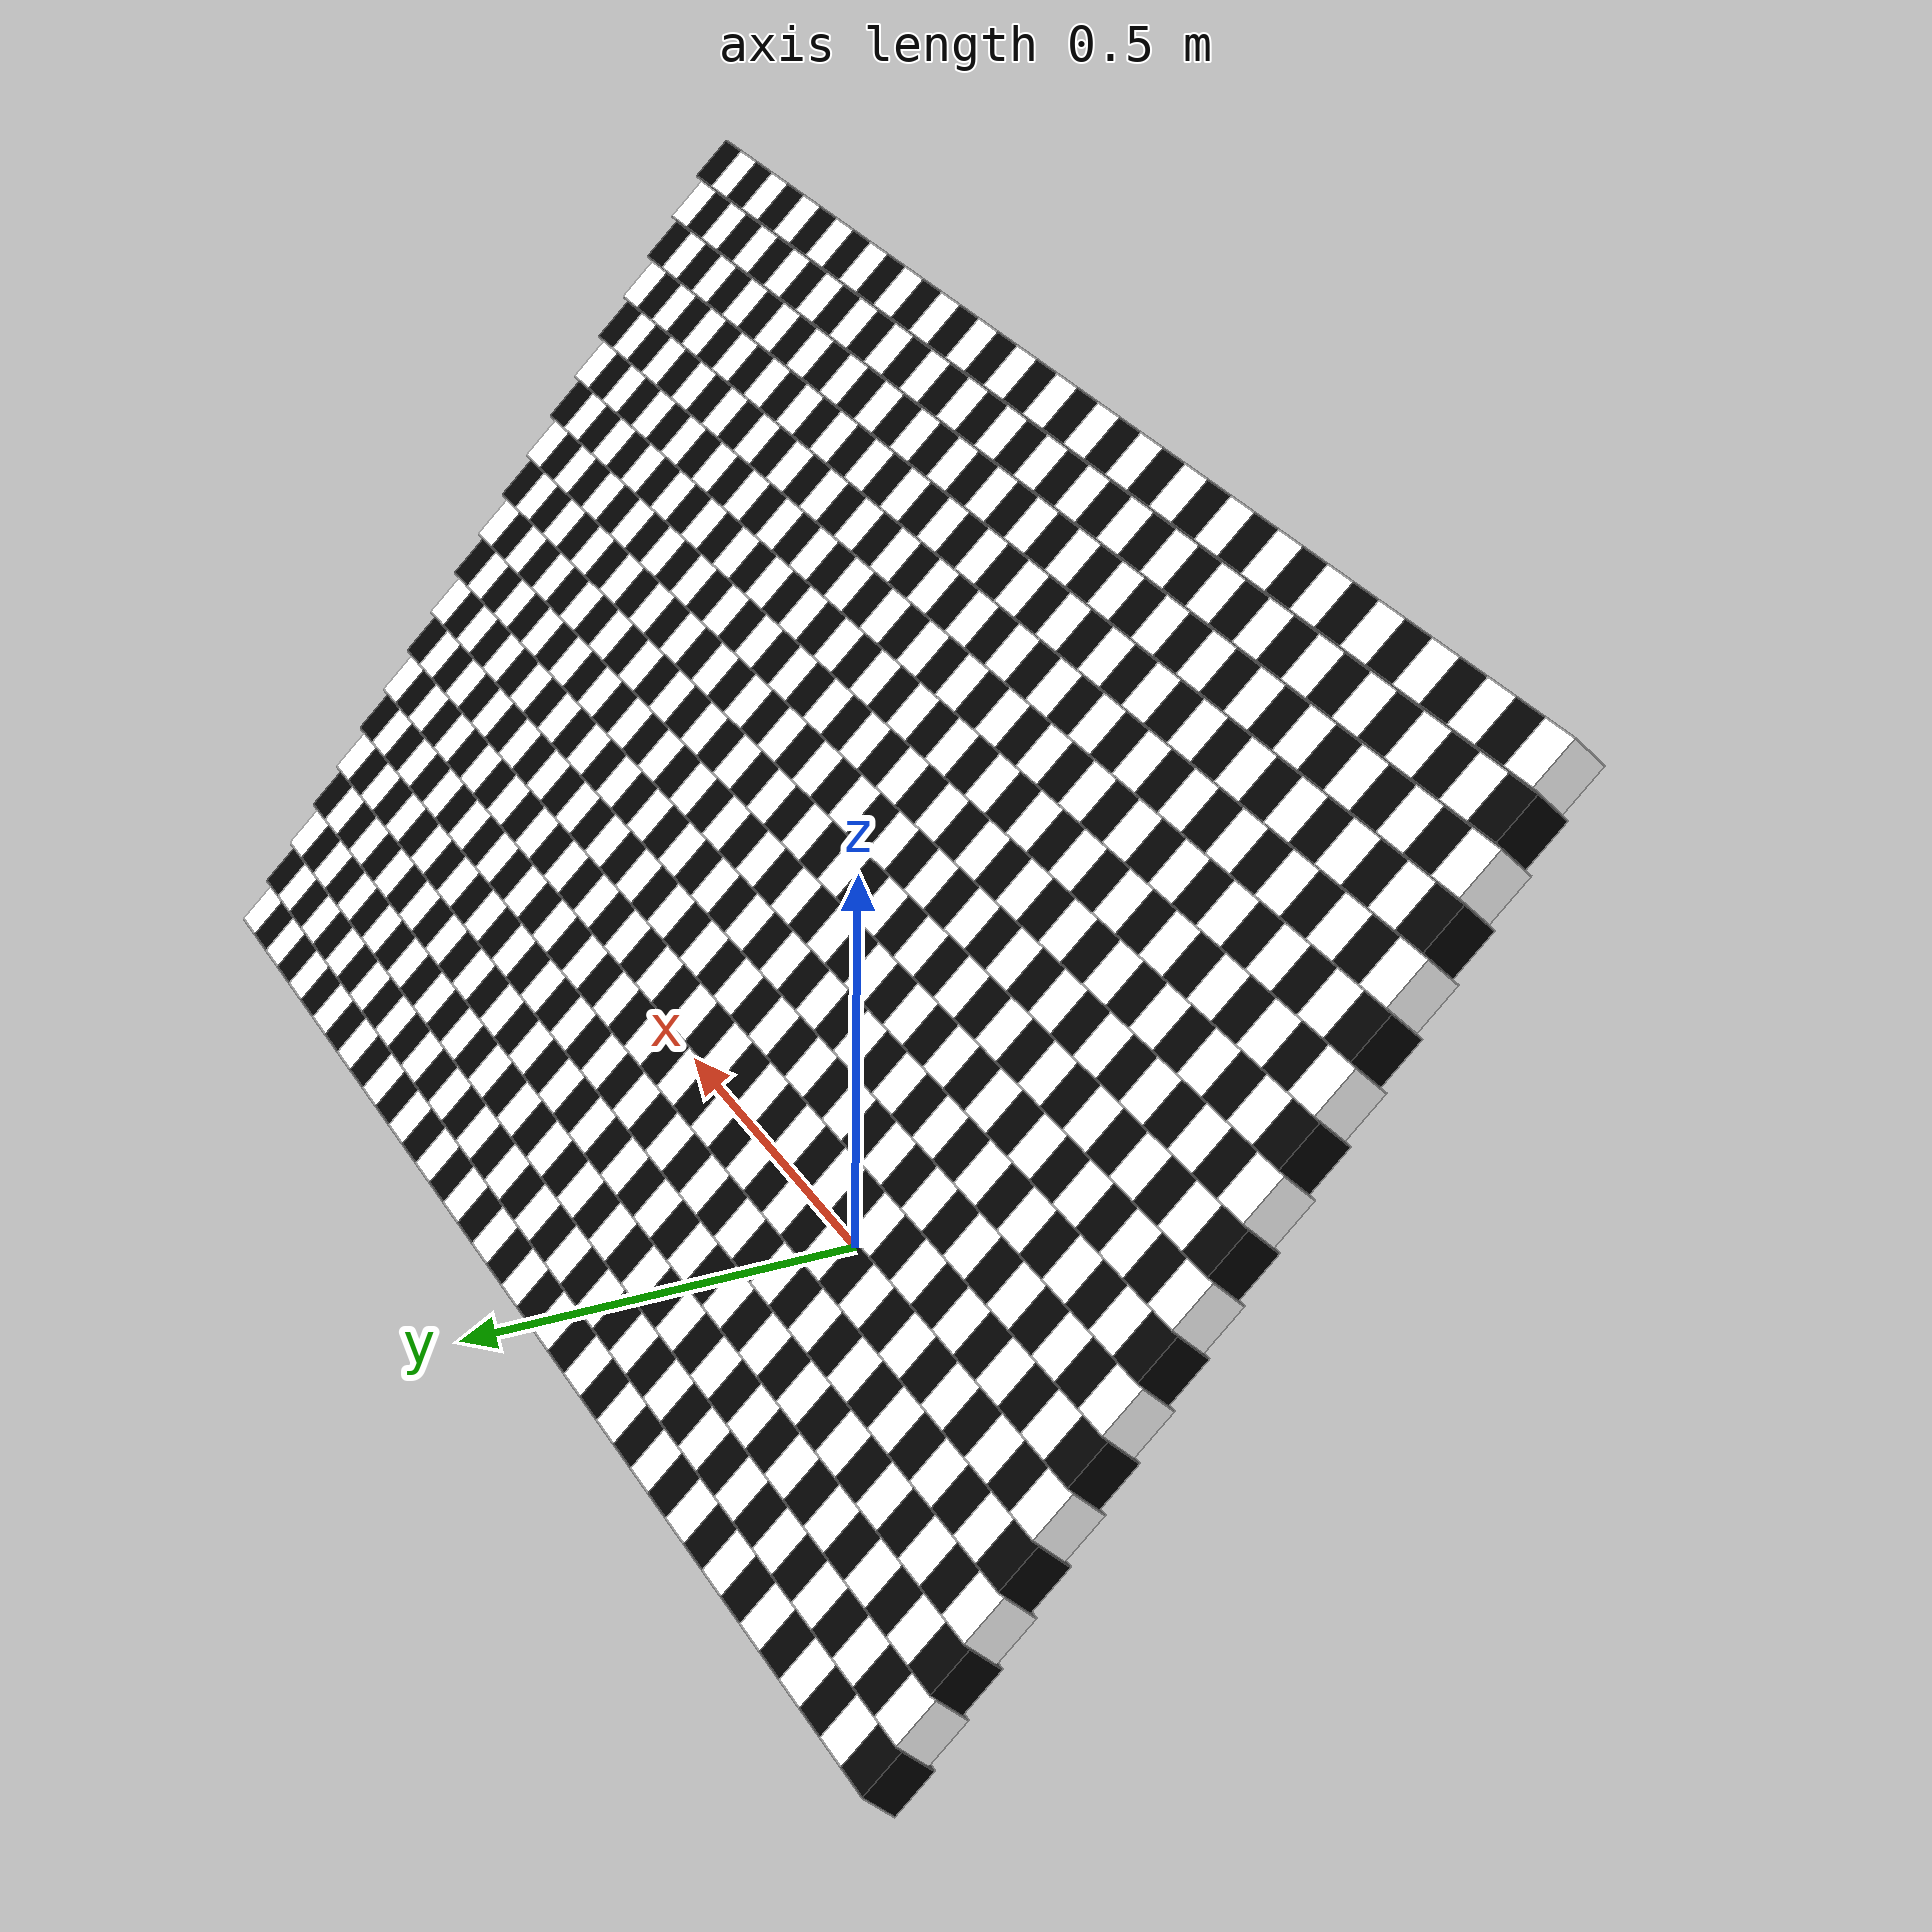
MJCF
<!-- This file was generated by build_angled_wall.py -->
<!-- It is not recommended to edit this file -->
<mujoco>
    <default>
        <geom density="100" friction=".5" rgba="1 .6 .8 1" />
    </default>
    <worldbody>
        <geom type="box" size=".025 .025 .03" pos="-0.95 -0.27175144212722024 1.0" euler="45 0 0" rgba="1 1 1 1" />
<geom type="box" size=".025 .025 .03" pos="-0.8999999999999999 -0.27175144212722024 1.0" euler="45 0 0" rgba="0 0 0 1" />
<geom type="box" size=".025 .025 .03" pos="-0.85 -0.27175144212722024 1.0" euler="45 0 0" rgba="1 1 1 1" />
<geom type="box" size=".025 .025 .03" pos="-0.7999999999999999 -0.27175144212722024 1.0" euler="45 0 0" rgba="0 0 0 1" />
<geom type="box" size=".025 .025 .03" pos="-0.75 -0.27175144212722024 1.0" euler="45 0 0" rgba="1 1 1 1" />
<geom type="box" size=".025 .025 .03" pos="-0.7 -0.27175144212722024 1.0" euler="45 0 0" rgba="0 0 0 1" />
<geom type="box" size=".025 .025 .03" pos="-0.6499999999999999 -0.27175144212722024 1.0" euler="45 0 0" rgba="1 1 1 1" />
<geom type="box" size=".025 .025 .03" pos="-0.5999999999999999 -0.27175144212722024 1.0" euler="45 0 0" rgba="0 0 0 1" />
<geom type="box" size=".025 .025 .03" pos="-0.5499999999999999 -0.27175144212722024 1.0" euler="45 0 0" rgba="1 1 1 1" />
<geom type="box" size=".025 .025 .03" pos="-0.49999999999999994 -0.27175144212722024 1.0" euler="45 0 0" rgba="0 0 0 1" />
<geom type="box" size=".025 .025 .03" pos="-0.44999999999999996 -0.27175144212722024 1.0" euler="45 0 0" rgba="1 1 1 1" />
<geom type="box" size=".025 .025 .03" pos="-0.3999999999999999 -0.27175144212722024 1.0" euler="45 0 0" rgba="0 0 0 1" />
<geom type="box" size=".025 .025 .03" pos="-0.34999999999999987 -0.27175144212722024 1.0" euler="45 0 0" rgba="1 1 1 1" />
<geom type="box" size=".025 .025 .03" pos="-0.29999999999999993 -0.27175144212722024 1.0" euler="45 0 0" rgba="0 0 0 1" />
<geom type="box" size=".025 .025 .03" pos="-0.2499999999999999 -0.27175144212722024 1.0" euler="45 0 0" rgba="1 1 1 1" />
<geom type="box" size=".025 .025 .03" pos="-0.19999999999999996 -0.27175144212722024 1.0" euler="45 0 0" rgba="0 0 0 1" />
<geom type="box" size=".025 .025 .03" pos="-0.1499999999999999 -0.27175144212722024 1.0" euler="45 0 0" rgba="1 1 1 1" />
<geom type="box" size=".025 .025 .03" pos="-0.09999999999999987 -0.27175144212722024 1.0" euler="45 0 0" rgba="0 0 0 1" />
<geom type="box" size=".025 .025 .03" pos="-0.04999999999999993 -0.27175144212722024 1.0" euler="45 0 0" rgba="1 1 1 1" />
<geom type="box" size=".025 .025 .03" pos="1.1102230246251565e-16 -0.27175144212722024 1.0" euler="45 0 0" rgba="0 0 0 1" />
<geom type="box" size=".025 .025 .03" pos="0.050000000000000044 -0.27175144212722024 1.0" euler="45 0 0" rgba="1 1 1 1" />
<geom type="box" size=".025 .025 .03" pos="0.10000000000000009 -0.27175144212722024 1.0" euler="45 0 0" rgba="0 0 0 1" />
<geom type="box" size=".025 .025 .03" pos="0.15000000000000013 -0.27175144212722024 1.0" euler="45 0 0" rgba="1 1 1 1" />
<geom type="box" size=".025 .025 .03" pos="0.20000000000000018 -0.27175144212722024 1.0" euler="45 0 0" rgba="0 0 0 1" />
<geom type="box" size=".025 .025 .03" pos="0.2500000000000002 -0.27175144212722024 1.0" euler="45 0 0" rgba="1 1 1 1" />
<geom type="box" size=".025 .025 .03" pos="0.30000000000000004 -0.27175144212722024 1.0" euler="45 0 0" rgba="0 0 0 1" />
<geom type="box" size=".025 .025 .03" pos="0.3500000000000001 -0.27175144212722024 1.0" euler="45 0 0" rgba="1 1 1 1" />
<geom type="box" size=".025 .025 .03" pos="0.40000000000000013 -0.27175144212722024 1.0" euler="45 0 0" rgba="0 0 0 1" />
<geom type="box" size=".025 .025 .03" pos="0.4500000000000002 -0.27175144212722024 1.0" euler="45 0 0" rgba="1 1 1 1" />
<geom type="box" size=".025 .025 .03" pos="0.5000000000000002 -0.27175144212722024 1.0" euler="45 0 0" rgba="0 0 0 1" />
<geom type="box" size=".025 .025 .03" pos="0.55 -0.27175144212722024 1.0" euler="45 0 0" rgba="1 1 1 1" />
<geom type="box" size=".025 .025 .03" pos="0.6000000000000001 -0.27175144212722024 1.0" euler="45 0 0" rgba="0 0 0 1" />
<geom type="box" size=".025 .025 .03" pos="0.6500000000000001 -0.27175144212722024 1.0" euler="45 0 0" rgba="1 1 1 1" />
<geom type="box" size=".025 .025 .03" pos="0.7000000000000002 -0.27175144212722024 1.0" euler="45 0 0" rgba="0 0 0 1" />
<geom type="box" size=".025 .025 .03" pos="0.7500000000000002 -0.27175144212722024 1.0" euler="45 0 0" rgba="1 1 1 1" />
<geom type="box" size=".025 .025 .03" pos="0.8 -0.27175144212722024 1.0" euler="45 0 0" rgba="0 0 0 1" />
<geom type="box" size=".025 .025 .03" pos="0.8500000000000001 -0.27175144212722024 1.0" euler="45 0 0" rgba="1 1 1 1" />
<geom type="box" size=".025 .025 .03" pos="0.9000000000000001 -0.27175144212722024 1.0" euler="45 0 0" rgba="0 0 0 1" />
<geom type="box" size=".025 .025 .03" pos="0.9500000000000002 -0.27175144212722024 1.0" euler="45 0 0" rgba="1 1 1 1" />
<geom type="box" size=".025 .025 .03" pos="1.0000000000000002 -0.27175144212722024 1.0" euler="45 0 0" rgba="0 0 0 1" />
<geom type="box" size=".025 .025 .03" pos="-0.95 -0.23639610306789288 0.95" euler="45 0 0" rgba="0 0 0 1" />
<geom type="box" size=".025 .025 .03" pos="-0.8999999999999999 -0.23639610306789288 0.95" euler="45 0 0" rgba="1 1 1 1" />
<geom type="box" size=".025 .025 .03" pos="-0.85 -0.23639610306789288 0.95" euler="45 0 0" rgba="0 0 0 1" />
<geom type="box" size=".025 .025 .03" pos="-0.7999999999999999 -0.23639610306789288 0.95" euler="45 0 0" rgba="1 1 1 1" />
<geom type="box" size=".025 .025 .03" pos="-0.75 -0.23639610306789288 0.95" euler="45 0 0" rgba="0 0 0 1" />
<geom type="box" size=".025 .025 .03" pos="-0.7 -0.23639610306789288 0.95" euler="45 0 0" rgba="1 1 1 1" />
<geom type="box" size=".025 .025 .03" pos="-0.6499999999999999 -0.23639610306789288 0.95" euler="45 0 0" rgba="0 0 0 1" />
<geom type="box" size=".025 .025 .03" pos="-0.5999999999999999 -0.23639610306789288 0.95" euler="45 0 0" rgba="1 1 1 1" />
<geom type="box" size=".025 .025 .03" pos="-0.5499999999999999 -0.23639610306789288 0.95" euler="45 0 0" rgba="0 0 0 1" />
<geom type="box" size=".025 .025 .03" pos="-0.49999999999999994 -0.23639610306789288 0.95" euler="45 0 0" rgba="1 1 1 1" />
<geom type="box" size=".025 .025 .03" pos="-0.44999999999999996 -0.23639610306789288 0.95" euler="45 0 0" rgba="0 0 0 1" />
<geom type="box" size=".025 .025 .03" pos="-0.3999999999999999 -0.23639610306789288 0.95" euler="45 0 0" rgba="1 1 1 1" />
<geom type="box" size=".025 .025 .03" pos="-0.34999999999999987 -0.23639610306789288 0.95" euler="45 0 0" rgba="0 0 0 1" />
<geom type="box" size=".025 .025 .03" pos="-0.29999999999999993 -0.23639610306789288 0.95" euler="45 0 0" rgba="1 1 1 1" />
<geom type="box" size=".025 .025 .03" pos="-0.2499999999999999 -0.23639610306789288 0.95" euler="45 0 0" rgba="0 0 0 1" />
<geom type="box" size=".025 .025 .03" pos="-0.19999999999999996 -0.23639610306789288 0.95" euler="45 0 0" rgba="1 1 1 1" />
<geom type="box" size=".025 .025 .03" pos="-0.1499999999999999 -0.23639610306789288 0.95" euler="45 0 0" rgba="0 0 0 1" />
<geom type="box" size=".025 .025 .03" pos="-0.09999999999999987 -0.23639610306789288 0.95" euler="45 0 0" rgba="1 1 1 1" />
<geom type="box" size=".025 .025 .03" pos="-0.04999999999999993 -0.23639610306789288 0.95" euler="45 0 0" rgba="0 0 0 1" />
<geom type="box" size=".025 .025 .03" pos="1.1102230246251565e-16 -0.23639610306789288 0.95" euler="45 0 0" rgba="1 1 1 1" />
<geom type="box" size=".025 .025 .03" pos="0.050000000000000044 -0.23639610306789288 0.95" euler="45 0 0" rgba="0 0 0 1" />
<geom type="box" size=".025 .025 .03" pos="0.10000000000000009 -0.23639610306789288 0.95" euler="45 0 0" rgba="1 1 1 1" />
<geom type="box" size=".025 .025 .03" pos="0.15000000000000013 -0.23639610306789288 0.95" euler="45 0 0" rgba="0 0 0 1" />
<geom type="box" size=".025 .025 .03" pos="0.20000000000000018 -0.23639610306789288 0.95" euler="45 0 0" rgba="1 1 1 1" />
<geom type="box" size=".025 .025 .03" pos="0.2500000000000002 -0.23639610306789288 0.95" euler="45 0 0" rgba="0 0 0 1" />
<geom type="box" size=".025 .025 .03" pos="0.30000000000000004 -0.23639610306789288 0.95" euler="45 0 0" rgba="1 1 1 1" />
<geom type="box" size=".025 .025 .03" pos="0.3500000000000001 -0.23639610306789288 0.95" euler="45 0 0" rgba="0 0 0 1" />
<geom type="box" size=".025 .025 .03" pos="0.40000000000000013 -0.23639610306789288 0.95" euler="45 0 0" rgba="1 1 1 1" />
<geom type="box" size=".025 .025 .03" pos="0.4500000000000002 -0.23639610306789288 0.95" euler="45 0 0" rgba="0 0 0 1" />
<geom type="box" size=".025 .025 .03" pos="0.5000000000000002 -0.23639610306789288 0.95" euler="45 0 0" rgba="1 1 1 1" />
<geom type="box" size=".025 .025 .03" pos="0.55 -0.23639610306789288 0.95" euler="45 0 0" rgba="0 0 0 1" />
<geom type="box" size=".025 .025 .03" pos="0.6000000000000001 -0.23639610306789288 0.95" euler="45 0 0" rgba="1 1 1 1" />
<geom type="box" size=".025 .025 .03" pos="0.6500000000000001 -0.23639610306789288 0.95" euler="45 0 0" rgba="0 0 0 1" />
<geom type="box" size=".025 .025 .03" pos="0.7000000000000002 -0.23639610306789288 0.95" euler="45 0 0" rgba="1 1 1 1" />
<geom type="box" size=".025 .025 .03" pos="0.7500000000000002 -0.23639610306789288 0.95" euler="45 0 0" rgba="0 0 0 1" />
<geom type="box" size=".025 .025 .03" pos="0.8 -0.23639610306789288 0.95" euler="45 0 0" rgba="1 1 1 1" />
<geom type="box" size=".025 .025 .03" pos="0.8500000000000001 -0.23639610306789288 0.95" euler="45 0 0" rgba="0 0 0 1" />
<geom type="box" size=".025 .025 .03" pos="0.9000000000000001 -0.23639610306789288 0.95" euler="45 0 0" rgba="1 1 1 1" />
<geom type="box" size=".025 .025 .03" pos="0.9500000000000002 -0.23639610306789288 0.95" euler="45 0 0" rgba="0 0 0 1" />
<geom type="box" size=".025 .025 .03" pos="1.0000000000000002 -0.23639610306789288 0.95" euler="45 0 0" rgba="1 1 1 1" />
<geom type="box" size=".025 .025 .03" pos="-0.95 -0.20104076400856546 0.9" euler="45 0 0" rgba="1 1 1 1" />
<geom type="box" size=".025 .025 .03" pos="-0.8999999999999999 -0.20104076400856546 0.9" euler="45 0 0" rgba="0 0 0 1" />
<geom type="box" size=".025 .025 .03" pos="-0.85 -0.20104076400856546 0.9" euler="45 0 0" rgba="1 1 1 1" />
<geom type="box" size=".025 .025 .03" pos="-0.7999999999999999 -0.20104076400856546 0.9" euler="45 0 0" rgba="0 0 0 1" />
<geom type="box" size=".025 .025 .03" pos="-0.75 -0.20104076400856546 0.9" euler="45 0 0" rgba="1 1 1 1" />
<geom type="box" size=".025 .025 .03" pos="-0.7 -0.20104076400856546 0.9" euler="45 0 0" rgba="0 0 0 1" />
<geom type="box" size=".025 .025 .03" pos="-0.6499999999999999 -0.20104076400856546 0.9" euler="45 0 0" rgba="1 1 1 1" />
<geom type="box" size=".025 .025 .03" pos="-0.5999999999999999 -0.20104076400856546 0.9" euler="45 0 0" rgba="0 0 0 1" />
<geom type="box" size=".025 .025 .03" pos="-0.5499999999999999 -0.20104076400856546 0.9" euler="45 0 0" rgba="1 1 1 1" />
<geom type="box" size=".025 .025 .03" pos="-0.49999999999999994 -0.20104076400856546 0.9" euler="45 0 0" rgba="0 0 0 1" />
<geom type="box" size=".025 .025 .03" pos="-0.44999999999999996 -0.20104076400856546 0.9" euler="45 0 0" rgba="1 1 1 1" />
<geom type="box" size=".025 .025 .03" pos="-0.3999999999999999 -0.20104076400856546 0.9" euler="45 0 0" rgba="0 0 0 1" />
<geom type="box" size=".025 .025 .03" pos="-0.34999999999999987 -0.20104076400856546 0.9" euler="45 0 0" rgba="1 1 1 1" />
<geom type="box" size=".025 .025 .03" pos="-0.29999999999999993 -0.20104076400856546 0.9" euler="45 0 0" rgba="0 0 0 1" />
<geom type="box" size=".025 .025 .03" pos="-0.2499999999999999 -0.20104076400856546 0.9" euler="45 0 0" rgba="1 1 1 1" />
<geom type="box" size=".025 .025 .03" pos="-0.19999999999999996 -0.20104076400856546 0.9" euler="45 0 0" rgba="0 0 0 1" />
<geom type="box" size=".025 .025 .03" pos="-0.1499999999999999 -0.20104076400856546 0.9" euler="45 0 0" rgba="1 1 1 1" />
<geom type="box" size=".025 .025 .03" pos="-0.09999999999999987 -0.20104076400856546 0.9" euler="45 0 0" rgba="0 0 0 1" />
<geom type="box" size=".025 .025 .03" pos="-0.04999999999999993 -0.20104076400856546 0.9" euler="45 0 0" rgba="1 1 1 1" />
<geom type="box" size=".025 .025 .03" pos="1.1102230246251565e-16 -0.20104076400856546 0.9" euler="45 0 0" rgba="0 0 0 1" />
<geom type="box" size=".025 .025 .03" pos="0.050000000000000044 -0.20104076400856546 0.9" euler="45 0 0" rgba="1 1 1 1" />
<geom type="box" size=".025 .025 .03" pos="0.10000000000000009 -0.20104076400856546 0.9" euler="45 0 0" rgba="0 0 0 1" />
<geom type="box" size=".025 .025 .03" pos="0.15000000000000013 -0.20104076400856546 0.9" euler="45 0 0" rgba="1 1 1 1" />
<geom type="box" size=".025 .025 .03" pos="0.20000000000000018 -0.20104076400856546 0.9" euler="45 0 0" rgba="0 0 0 1" />
<geom type="box" size=".025 .025 .03" pos="0.2500000000000002 -0.20104076400856546 0.9" euler="45 0 0" rgba="1 1 1 1" />
<geom type="box" size=".025 .025 .03" pos="0.30000000000000004 -0.20104076400856546 0.9" euler="45 0 0" rgba="0 0 0 1" />
<geom type="box" size=".025 .025 .03" pos="0.3500000000000001 -0.20104076400856546 0.9" euler="45 0 0" rgba="1 1 1 1" />
<geom type="box" size=".025 .025 .03" pos="0.40000000000000013 -0.20104076400856546 0.9" euler="45 0 0" rgba="0 0 0 1" />
<geom type="box" size=".025 .025 .03" pos="0.4500000000000002 -0.20104076400856546 0.9" euler="45 0 0" rgba="1 1 1 1" />
<geom type="box" size=".025 .025 .03" pos="0.5000000000000002 -0.20104076400856546 0.9" euler="45 0 0" rgba="0 0 0 1" />
<geom type="box" size=".025 .025 .03" pos="0.55 -0.20104076400856546 0.9" euler="45 0 0" rgba="1 1 1 1" />
<geom type="box" size=".025 .025 .03" pos="0.6000000000000001 -0.20104076400856546 0.9" euler="45 0 0" rgba="0 0 0 1" />
<geom type="box" size=".025 .025 .03" pos="0.6500000000000001 -0.20104076400856546 0.9" euler="45 0 0" rgba="1 1 1 1" />
<geom type="box" size=".025 .025 .03" pos="0.7000000000000002 -0.20104076400856546 0.9" euler="45 0 0" rgba="0 0 0 1" />
<geom type="box" size=".025 .025 .03" pos="0.7500000000000002 -0.20104076400856546 0.9" euler="45 0 0" rgba="1 1 1 1" />
<geom type="box" size=".025 .025 .03" pos="0.8 -0.20104076400856546 0.9" euler="45 0 0" rgba="0 0 0 1" />
<geom type="box" size=".025 .025 .03" pos="0.8500000000000001 -0.20104076400856546 0.9" euler="45 0 0" rgba="1 1 1 1" />
<geom type="box" size=".025 .025 .03" pos="0.9000000000000001 -0.20104076400856546 0.9" euler="45 0 0" rgba="0 0 0 1" />
<geom type="box" size=".025 .025 .03" pos="0.9500000000000002 -0.20104076400856546 0.9" euler="45 0 0" rgba="1 1 1 1" />
<geom type="box" size=".025 .025 .03" pos="1.0000000000000002 -0.20104076400856546 0.9" euler="45 0 0" rgba="0 0 0 1" />
<geom type="box" size=".025 .025 .03" pos="-0.95 -0.1656854249492381 0.85" euler="45 0 0" rgba="0 0 0 1" />
<geom type="box" size=".025 .025 .03" pos="-0.8999999999999999 -0.1656854249492381 0.85" euler="45 0 0" rgba="1 1 1 1" />
<geom type="box" size=".025 .025 .03" pos="-0.85 -0.1656854249492381 0.85" euler="45 0 0" rgba="0 0 0 1" />
<geom type="box" size=".025 .025 .03" pos="-0.7999999999999999 -0.1656854249492381 0.85" euler="45 0 0" rgba="1 1 1 1" />
<geom type="box" size=".025 .025 .03" pos="-0.75 -0.1656854249492381 0.85" euler="45 0 0" rgba="0 0 0 1" />
<geom type="box" size=".025 .025 .03" pos="-0.7 -0.1656854249492381 0.85" euler="45 0 0" rgba="1 1 1 1" />
<geom type="box" size=".025 .025 .03" pos="-0.6499999999999999 -0.1656854249492381 0.85" euler="45 0 0" rgba="0 0 0 1" />
<geom type="box" size=".025 .025 .03" pos="-0.5999999999999999 -0.1656854249492381 0.85" euler="45 0 0" rgba="1 1 1 1" />
<geom type="box" size=".025 .025 .03" pos="-0.5499999999999999 -0.1656854249492381 0.85" euler="45 0 0" rgba="0 0 0 1" />
<geom type="box" size=".025 .025 .03" pos="-0.49999999999999994 -0.1656854249492381 0.85" euler="45 0 0" rgba="1 1 1 1" />
<geom type="box" size=".025 .025 .03" pos="-0.44999999999999996 -0.1656854249492381 0.85" euler="45 0 0" rgba="0 0 0 1" />
<geom type="box" size=".025 .025 .03" pos="-0.3999999999999999 -0.1656854249492381 0.85" euler="45 0 0" rgba="1 1 1 1" />
<geom type="box" size=".025 .025 .03" pos="-0.34999999999999987 -0.1656854249492381 0.85" euler="45 0 0" rgba="0 0 0 1" />
<geom type="box" size=".025 .025 .03" pos="-0.29999999999999993 -0.1656854249492381 0.85" euler="45 0 0" rgba="1 1 1 1" />
<geom type="box" size=".025 .025 .03" pos="-0.2499999999999999 -0.1656854249492381 0.85" euler="45 0 0" rgba="0 0 0 1" />
<geom type="box" size=".025 .025 .03" pos="-0.19999999999999996 -0.1656854249492381 0.85" euler="45 0 0" rgba="1 1 1 1" />
<geom type="box" size=".025 .025 .03" pos="-0.1499999999999999 -0.1656854249492381 0.85" euler="45 0 0" rgba="0 0 0 1" />
<geom type="box" size=".025 .025 .03" pos="-0.09999999999999987 -0.1656854249492381 0.85" euler="45 0 0" rgba="1 1 1 1" />
<geom type="box" size=".025 .025 .03" pos="-0.04999999999999993 -0.1656854249492381 0.85" euler="45 0 0" rgba="0 0 0 1" />
<geom type="box" size=".025 .025 .03" pos="1.1102230246251565e-16 -0.1656854249492381 0.85" euler="45 0 0" rgba="1 1 1 1" />
<geom type="box" size=".025 .025 .03" pos="0.050000000000000044 -0.1656854249492381 0.85" euler="45 0 0" rgba="0 0 0 1" />
<geom type="box" size=".025 .025 .03" pos="0.10000000000000009 -0.1656854249492381 0.85" euler="45 0 0" rgba="1 1 1 1" />
<geom type="box" size=".025 .025 .03" pos="0.15000000000000013 -0.1656854249492381 0.85" euler="45 0 0" rgba="0 0 0 1" />
<geom type="box" size=".025 .025 .03" pos="0.20000000000000018 -0.1656854249492381 0.85" euler="45 0 0" rgba="1 1 1 1" />
<geom type="box" size=".025 .025 .03" pos="0.2500000000000002 -0.1656854249492381 0.85" euler="45 0 0" rgba="0 0 0 1" />
<geom type="box" size=".025 .025 .03" pos="0.30000000000000004 -0.1656854249492381 0.85" euler="45 0 0" rgba="1 1 1 1" />
<geom type="box" size=".025 .025 .03" pos="0.3500000000000001 -0.1656854249492381 0.85" euler="45 0 0" rgba="0 0 0 1" />
<geom type="box" size=".025 .025 .03" pos="0.40000000000000013 -0.1656854249492381 0.85" euler="45 0 0" rgba="1 1 1 1" />
<geom type="box" size=".025 .025 .03" pos="0.4500000000000002 -0.1656854249492381 0.85" euler="45 0 0" rgba="0 0 0 1" />
<geom type="box" size=".025 .025 .03" pos="0.5000000000000002 -0.1656854249492381 0.85" euler="45 0 0" rgba="1 1 1 1" />
<geom type="box" size=".025 .025 .03" pos="0.55 -0.1656854249492381 0.85" euler="45 0 0" rgba="0 0 0 1" />
<geom type="box" size=".025 .025 .03" pos="0.6000000000000001 -0.1656854249492381 0.85" euler="45 0 0" rgba="1 1 1 1" />
<geom type="box" size=".025 .025 .03" pos="0.6500000000000001 -0.1656854249492381 0.85" euler="45 0 0" rgba="0 0 0 1" />
<geom type="box" size=".025 .025 .03" pos="0.7000000000000002 -0.1656854249492381 0.85" euler="45 0 0" rgba="1 1 1 1" />
<geom type="box" size=".025 .025 .03" pos="0.7500000000000002 -0.1656854249492381 0.85" euler="45 0 0" rgba="0 0 0 1" />
<geom type="box" size=".025 .025 .03" pos="0.8 -0.1656854249492381 0.85" euler="45 0 0" rgba="1 1 1 1" />
<geom type="box" size=".025 .025 .03" pos="0.8500000000000001 -0.1656854249492381 0.85" euler="45 0 0" rgba="0 0 0 1" />
<geom type="box" size=".025 .025 .03" pos="0.9000000000000001 -0.1656854249492381 0.85" euler="45 0 0" rgba="1 1 1 1" />
<geom type="box" size=".025 .025 .03" pos="0.9500000000000002 -0.1656854249492381 0.85" euler="45 0 0" rgba="0 0 0 1" />
<geom type="box" size=".025 .025 .03" pos="1.0000000000000002 -0.1656854249492381 0.85" euler="45 0 0" rgba="1 1 1 1" />
<geom type="box" size=".025 .025 .03" pos="-0.95 -0.13033008588991069 0.8" euler="45 0 0" rgba="1 1 1 1" />
<geom type="box" size=".025 .025 .03" pos="-0.8999999999999999 -0.13033008588991069 0.8" euler="45 0 0" rgba="0 0 0 1" />
<geom type="box" size=".025 .025 .03" pos="-0.85 -0.13033008588991069 0.8" euler="45 0 0" rgba="1 1 1 1" />
<geom type="box" size=".025 .025 .03" pos="-0.7999999999999999 -0.13033008588991069 0.8" euler="45 0 0" rgba="0 0 0 1" />
<geom type="box" size=".025 .025 .03" pos="-0.75 -0.13033008588991069 0.8" euler="45 0 0" rgba="1 1 1 1" />
<geom type="box" size=".025 .025 .03" pos="-0.7 -0.13033008588991069 0.8" euler="45 0 0" rgba="0 0 0 1" />
<geom type="box" size=".025 .025 .03" pos="-0.6499999999999999 -0.13033008588991069 0.8" euler="45 0 0" rgba="1 1 1 1" />
<geom type="box" size=".025 .025 .03" pos="-0.5999999999999999 -0.13033008588991069 0.8" euler="45 0 0" rgba="0 0 0 1" />
<geom type="box" size=".025 .025 .03" pos="-0.5499999999999999 -0.13033008588991069 0.8" euler="45 0 0" rgba="1 1 1 1" />
<geom type="box" size=".025 .025 .03" pos="-0.49999999999999994 -0.13033008588991069 0.8" euler="45 0 0" rgba="0 0 0 1" />
<geom type="box" size=".025 .025 .03" pos="-0.44999999999999996 -0.13033008588991069 0.8" euler="45 0 0" rgba="1 1 1 1" />
<geom type="box" size=".025 .025 .03" pos="-0.3999999999999999 -0.13033008588991069 0.8" euler="45 0 0" rgba="0 0 0 1" />
<geom type="box" size=".025 .025 .03" pos="-0.34999999999999987 -0.13033008588991069 0.8" euler="45 0 0" rgba="1 1 1 1" />
<geom type="box" size=".025 .025 .03" pos="-0.29999999999999993 -0.13033008588991069 0.8" euler="45 0 0" rgba="0 0 0 1" />
<geom type="box" size=".025 .025 .03" pos="-0.2499999999999999 -0.13033008588991069 0.8" euler="45 0 0" rgba="1 1 1 1" />
<geom type="box" size=".025 .025 .03" pos="-0.19999999999999996 -0.13033008588991069 0.8" euler="45 0 0" rgba="0 0 0 1" />
<geom type="box" size=".025 .025 .03" pos="-0.1499999999999999 -0.13033008588991069 0.8" euler="45 0 0" rgba="1 1 1 1" />
<geom type="box" size=".025 .025 .03" pos="-0.09999999999999987 -0.13033008588991069 0.8" euler="45 0 0" rgba="0 0 0 1" />
<geom type="box" size=".025 .025 .03" pos="-0.04999999999999993 -0.13033008588991069 0.8" euler="45 0 0" rgba="1 1 1 1" />
<geom type="box" size=".025 .025 .03" pos="1.1102230246251565e-16 -0.13033008588991069 0.8" euler="45 0 0" rgba="0 0 0 1" />
<geom type="box" size=".025 .025 .03" pos="0.050000000000000044 -0.13033008588991069 0.8" euler="45 0 0" rgba="1 1 1 1" />
<geom type="box" size=".025 .025 .03" pos="0.10000000000000009 -0.13033008588991069 0.8" euler="45 0 0" rgba="0 0 0 1" />
<geom type="box" size=".025 .025 .03" pos="0.15000000000000013 -0.13033008588991069 0.8" euler="45 0 0" rgba="1 1 1 1" />
<geom type="box" size=".025 .025 .03" pos="0.20000000000000018 -0.13033008588991069 0.8" euler="45 0 0" rgba="0 0 0 1" />
<geom type="box" size=".025 .025 .03" pos="0.2500000000000002 -0.13033008588991069 0.8" euler="45 0 0" rgba="1 1 1 1" />
<geom type="box" size=".025 .025 .03" pos="0.30000000000000004 -0.13033008588991069 0.8" euler="45 0 0" rgba="0 0 0 1" />
<geom type="box" size=".025 .025 .03" pos="0.3500000000000001 -0.13033008588991069 0.8" euler="45 0 0" rgba="1 1 1 1" />
<geom type="box" size=".025 .025 .03" pos="0.40000000000000013 -0.13033008588991069 0.8" euler="45 0 0" rgba="0 0 0 1" />
<geom type="box" size=".025 .025 .03" pos="0.4500000000000002 -0.13033008588991069 0.8" euler="45 0 0" rgba="1 1 1 1" />
<geom type="box" size=".025 .025 .03" pos="0.5000000000000002 -0.13033008588991069 0.8" euler="45 0 0" rgba="0 0 0 1" />
<geom type="box" size=".025 .025 .03" pos="0.55 -0.13033008588991069 0.8" euler="45 0 0" rgba="1 1 1 1" />
<geom type="box" size=".025 .025 .03" pos="0.6000000000000001 -0.13033008588991069 0.8" euler="45 0 0" rgba="0 0 0 1" />
<geom type="box" size=".025 .025 .03" pos="0.6500000000000001 -0.13033008588991069 0.8" euler="45 0 0" rgba="1 1 1 1" />
<geom type="box" size=".025 .025 .03" pos="0.7000000000000002 -0.13033008588991069 0.8" euler="45 0 0" rgba="0 0 0 1" />
<geom type="box" size=".025 .025 .03" pos="0.7500000000000002 -0.13033008588991069 0.8" euler="45 0 0" rgba="1 1 1 1" />
<geom type="box" size=".025 .025 .03" pos="0.8 -0.13033008588991069 0.8" euler="45 0 0" rgba="0 0 0 1" />
<geom type="box" size=".025 .025 .03" pos="0.8500000000000001 -0.13033008588991069 0.8" euler="45 0 0" rgba="1 1 1 1" />
<geom type="box" size=".025 .025 .03" pos="0.9000000000000001 -0.13033008588991069 0.8" euler="45 0 0" rgba="0 0 0 1" />
<geom type="box" size=".025 .025 .03" pos="0.9500000000000002 -0.13033008588991069 0.8" euler="45 0 0" rgba="1 1 1 1" />
<geom type="box" size=".025 .025 .03" pos="1.0000000000000002 -0.13033008588991069 0.8" euler="45 0 0" rgba="0 0 0 1" />
<geom type="box" size=".025 .025 .03" pos="-0.95 -0.09497474683058338 0.75" euler="45 0 0" rgba="0 0 0 1" />
<geom type="box" size=".025 .025 .03" pos="-0.8999999999999999 -0.09497474683058338 0.75" euler="45 0 0" rgba="1 1 1 1" />
<geom type="box" size=".025 .025 .03" pos="-0.85 -0.09497474683058338 0.75" euler="45 0 0" rgba="0 0 0 1" />
<geom type="box" size=".025 .025 .03" pos="-0.7999999999999999 -0.09497474683058338 0.75" euler="45 0 0" rgba="1 1 1 1" />
<geom type="box" size=".025 .025 .03" pos="-0.75 -0.09497474683058338 0.75" euler="45 0 0" rgba="0 0 0 1" />
<geom type="box" size=".025 .025 .03" pos="-0.7 -0.09497474683058338 0.75" euler="45 0 0" rgba="1 1 1 1" />
<geom type="box" size=".025 .025 .03" pos="-0.6499999999999999 -0.09497474683058338 0.75" euler="45 0 0" rgba="0 0 0 1" />
<geom type="box" size=".025 .025 .03" pos="-0.5999999999999999 -0.09497474683058338 0.75" euler="45 0 0" rgba="1 1 1 1" />
<geom type="box" size=".025 .025 .03" pos="-0.5499999999999999 -0.09497474683058338 0.75" euler="45 0 0" rgba="0 0 0 1" />
<geom type="box" size=".025 .025 .03" pos="-0.49999999999999994 -0.09497474683058338 0.75" euler="45 0 0" rgba="1 1 1 1" />
<geom type="box" size=".025 .025 .03" pos="-0.44999999999999996 -0.09497474683058338 0.75" euler="45 0 0" rgba="0 0 0 1" />
<geom type="box" size=".025 .025 .03" pos="-0.3999999999999999 -0.09497474683058338 0.75" euler="45 0 0" rgba="1 1 1 1" />
<geom type="box" size=".025 .025 .03" pos="-0.34999999999999987 -0.09497474683058338 0.75" euler="45 0 0" rgba="0 0 0 1" />
<geom type="box" size=".025 .025 .03" pos="-0.29999999999999993 -0.09497474683058338 0.75" euler="45 0 0" rgba="1 1 1 1" />
<geom type="box" size=".025 .025 .03" pos="-0.2499999999999999 -0.09497474683058338 0.75" euler="45 0 0" rgba="0 0 0 1" />
<geom type="box" size=".025 .025 .03" pos="-0.19999999999999996 -0.09497474683058338 0.75" euler="45 0 0" rgba="1 1 1 1" />
<geom type="box" size=".025 .025 .03" pos="-0.1499999999999999 -0.09497474683058338 0.75" euler="45 0 0" rgba="0 0 0 1" />
<geom type="box" size=".025 .025 .03" pos="-0.09999999999999987 -0.09497474683058338 0.75" euler="45 0 0" rgba="1 1 1 1" />
<geom type="box" size=".025 .025 .03" pos="-0.04999999999999993 -0.09497474683058338 0.75" euler="45 0 0" rgba="0 0 0 1" />
<geom type="box" size=".025 .025 .03" pos="1.1102230246251565e-16 -0.09497474683058338 0.75" euler="45 0 0" rgba="1 1 1 1" />
<geom type="box" size=".025 .025 .03" pos="0.050000000000000044 -0.09497474683058338 0.75" euler="45 0 0" rgba="0 0 0 1" />
<geom type="box" size=".025 .025 .03" pos="0.10000000000000009 -0.09497474683058338 0.75" euler="45 0 0" rgba="1 1 1 1" />
<geom type="box" size=".025 .025 .03" pos="0.15000000000000013 -0.09497474683058338 0.75" euler="45 0 0" rgba="0 0 0 1" />
<geom type="box" size=".025 .025 .03" pos="0.20000000000000018 -0.09497474683058338 0.75" euler="45 0 0" rgba="1 1 1 1" />
<geom type="box" size=".025 .025 .03" pos="0.2500000000000002 -0.09497474683058338 0.75" euler="45 0 0" rgba="0 0 0 1" />
<geom type="box" size=".025 .025 .03" pos="0.30000000000000004 -0.09497474683058338 0.75" euler="45 0 0" rgba="1 1 1 1" />
<geom type="box" size=".025 .025 .03" pos="0.3500000000000001 -0.09497474683058338 0.75" euler="45 0 0" rgba="0 0 0 1" />
<geom type="box" size=".025 .025 .03" pos="0.40000000000000013 -0.09497474683058338 0.75" euler="45 0 0" rgba="1 1 1 1" />
<geom type="box" size=".025 .025 .03" pos="0.4500000000000002 -0.09497474683058338 0.75" euler="45 0 0" rgba="0 0 0 1" />
<geom type="box" size=".025 .025 .03" pos="0.5000000000000002 -0.09497474683058338 0.75" euler="45 0 0" rgba="1 1 1 1" />
<geom type="box" size=".025 .025 .03" pos="0.55 -0.09497474683058338 0.75" euler="45 0 0" rgba="0 0 0 1" />
<geom type="box" size=".025 .025 .03" pos="0.6000000000000001 -0.09497474683058338 0.75" euler="45 0 0" rgba="1 1 1 1" />
<geom type="box" size=".025 .025 .03" pos="0.6500000000000001 -0.09497474683058338 0.75" euler="45 0 0" rgba="0 0 0 1" />
<geom type="box" size=".025 .025 .03" pos="0.7000000000000002 -0.09497474683058338 0.75" euler="45 0 0" rgba="1 1 1 1" />
<geom type="box" size=".025 .025 .03" pos="0.7500000000000002 -0.09497474683058338 0.75" euler="45 0 0" rgba="0 0 0 1" />
<geom type="box" size=".025 .025 .03" pos="0.8 -0.09497474683058338 0.75" euler="45 0 0" rgba="1 1 1 1" />
<geom type="box" size=".025 .025 .03" pos="0.8500000000000001 -0.09497474683058338 0.75" euler="45 0 0" rgba="0 0 0 1" />
<geom type="box" size=".025 .025 .03" pos="0.9000000000000001 -0.09497474683058338 0.75" euler="45 0 0" rgba="1 1 1 1" />
<geom type="box" size=".025 .025 .03" pos="0.9500000000000002 -0.09497474683058338 0.75" euler="45 0 0" rgba="0 0 0 1" />
<geom type="box" size=".025 .025 .03" pos="1.0000000000000002 -0.09497474683058338 0.75" euler="45 0 0" rgba="1 1 1 1" />
<geom type="box" size=".025 .025 .03" pos="-0.95 -0.05961940777125596 0.7" euler="45 0 0" rgba="1 1 1 1" />
<geom type="box" size=".025 .025 .03" pos="-0.8999999999999999 -0.05961940777125596 0.7" euler="45 0 0" rgba="0 0 0 1" />
<geom type="box" size=".025 .025 .03" pos="-0.85 -0.05961940777125596 0.7" euler="45 0 0" rgba="1 1 1 1" />
<geom type="box" size=".025 .025 .03" pos="-0.7999999999999999 -0.05961940777125596 0.7" euler="45 0 0" rgba="0 0 0 1" />
<geom type="box" size=".025 .025 .03" pos="-0.75 -0.05961940777125596 0.7" euler="45 0 0" rgba="1 1 1 1" />
<geom type="box" size=".025 .025 .03" pos="-0.7 -0.05961940777125596 0.7" euler="45 0 0" rgba="0 0 0 1" />
<geom type="box" size=".025 .025 .03" pos="-0.6499999999999999 -0.05961940777125596 0.7" euler="45 0 0" rgba="1 1 1 1" />
<geom type="box" size=".025 .025 .03" pos="-0.5999999999999999 -0.05961940777125596 0.7" euler="45 0 0" rgba="0 0 0 1" />
<geom type="box" size=".025 .025 .03" pos="-0.5499999999999999 -0.05961940777125596 0.7" euler="45 0 0" rgba="1 1 1 1" />
<geom type="box" size=".025 .025 .03" pos="-0.49999999999999994 -0.05961940777125596 0.7" euler="45 0 0" rgba="0 0 0 1" />
<geom type="box" size=".025 .025 .03" pos="-0.44999999999999996 -0.05961940777125596 0.7" euler="45 0 0" rgba="1 1 1 1" />
<geom type="box" size=".025 .025 .03" pos="-0.3999999999999999 -0.05961940777125596 0.7" euler="45 0 0" rgba="0 0 0 1" />
<geom type="box" size=".025 .025 .03" pos="-0.34999999999999987 -0.05961940777125596 0.7" euler="45 0 0" rgba="1 1 1 1" />
<geom type="box" size=".025 .025 .03" pos="-0.29999999999999993 -0.05961940777125596 0.7" euler="45 0 0" rgba="0 0 0 1" />
<geom type="box" size=".025 .025 .03" pos="-0.2499999999999999 -0.05961940777125596 0.7" euler="45 0 0" rgba="1 1 1 1" />
<geom type="box" size=".025 .025 .03" pos="-0.19999999999999996 -0.05961940777125596 0.7" euler="45 0 0" rgba="0 0 0 1" />
<geom type="box" size=".025 .025 .03" pos="-0.1499999999999999 -0.05961940777125596 0.7" euler="45 0 0" rgba="1 1 1 1" />
<geom type="box" size=".025 .025 .03" pos="-0.09999999999999987 -0.05961940777125596 0.7" euler="45 0 0" rgba="0 0 0 1" />
<geom type="box" size=".025 .025 .03" pos="-0.04999999999999993 -0.05961940777125596 0.7" euler="45 0 0" rgba="1 1 1 1" />
<geom type="box" size=".025 .025 .03" pos="1.1102230246251565e-16 -0.05961940777125596 0.7" euler="45 0 0" rgba="0 0 0 1" />
<geom type="box" size=".025 .025 .03" pos="0.050000000000000044 -0.05961940777125596 0.7" euler="45 0 0" rgba="1 1 1 1" />
<geom type="box" size=".025 .025 .03" pos="0.10000000000000009 -0.05961940777125596 0.7" euler="45 0 0" rgba="0 0 0 1" />
<geom type="box" size=".025 .025 .03" pos="0.15000000000000013 -0.05961940777125596 0.7" euler="45 0 0" rgba="1 1 1 1" />
<geom type="box" size=".025 .025 .03" pos="0.20000000000000018 -0.05961940777125596 0.7" euler="45 0 0" rgba="0 0 0 1" />
<geom type="box" size=".025 .025 .03" pos="0.2500000000000002 -0.05961940777125596 0.7" euler="45 0 0" rgba="1 1 1 1" />
<geom type="box" size=".025 .025 .03" pos="0.30000000000000004 -0.05961940777125596 0.7" euler="45 0 0" rgba="0 0 0 1" />
<geom type="box" size=".025 .025 .03" pos="0.3500000000000001 -0.05961940777125596 0.7" euler="45 0 0" rgba="1 1 1 1" />
<geom type="box" size=".025 .025 .03" pos="0.40000000000000013 -0.05961940777125596 0.7" euler="45 0 0" rgba="0 0 0 1" />
<geom type="box" size=".025 .025 .03" pos="0.4500000000000002 -0.05961940777125596 0.7" euler="45 0 0" rgba="1 1 1 1" />
<geom type="box" size=".025 .025 .03" pos="0.5000000000000002 -0.05961940777125596 0.7" euler="45 0 0" rgba="0 0 0 1" />
<geom type="box" size=".025 .025 .03" pos="0.55 -0.05961940777125596 0.7" euler="45 0 0" rgba="1 1 1 1" />
<geom type="box" size=".025 .025 .03" pos="0.6000000000000001 -0.05961940777125596 0.7" euler="45 0 0" rgba="0 0 0 1" />
<geom type="box" size=".025 .025 .03" pos="0.6500000000000001 -0.05961940777125596 0.7" euler="45 0 0" rgba="1 1 1 1" />
<geom type="box" size=".025 .025 .03" pos="0.7000000000000002 -0.05961940777125596 0.7" euler="45 0 0" rgba="0 0 0 1" />
<geom type="box" size=".025 .025 .03" pos="0.7500000000000002 -0.05961940777125596 0.7" euler="45 0 0" rgba="1 1 1 1" />
<geom type="box" size=".025 .025 .03" pos="0.8 -0.05961940777125596 0.7" euler="45 0 0" rgba="0 0 0 1" />
<geom type="box" size=".025 .025 .03" pos="0.8500000000000001 -0.05961940777125596 0.7" euler="45 0 0" rgba="1 1 1 1" />
<geom type="box" size=".025 .025 .03" pos="0.9000000000000001 -0.05961940777125596 0.7" euler="45 0 0" rgba="0 0 0 1" />
<geom type="box" size=".025 .025 .03" pos="0.9500000000000002 -0.05961940777125596 0.7" euler="45 0 0" rgba="1 1 1 1" />
<geom type="box" size=".025 .025 .03" pos="1.0000000000000002 -0.05961940777125596 0.7" euler="45 0 0" rgba="0 0 0 1" />
<geom type="box" size=".025 .025 .03" pos="-0.95 -0.024264068711928544 0.6499999999999999" euler="45 0 0" rgba="0 0 0 1" />
<geom type="box" size=".025 .025 .03" pos="-0.8999999999999999 -0.024264068711928544 0.6499999999999999" euler="45 0 0" rgba="1 1 1 1" />
<geom type="box" size=".025 .025 .03" pos="-0.85 -0.024264068711928544 0.6499999999999999" euler="45 0 0" rgba="0 0 0 1" />
<geom type="box" size=".025 .025 .03" pos="-0.7999999999999999 -0.024264068711928544 0.6499999999999999" euler="45 0 0" rgba="1 1 1 1" />
<geom type="box" size=".025 .025 .03" pos="-0.75 -0.024264068711928544 0.6499999999999999" euler="45 0 0" rgba="0 0 0 1" />
<geom type="box" size=".025 .025 .03" pos="-0.7 -0.024264068711928544 0.6499999999999999" euler="45 0 0" rgba="1 1 1 1" />
<geom type="box" size=".025 .025 .03" pos="-0.6499999999999999 -0.024264068711928544 0.6499999999999999" euler="45 0 0" rgba="0 0 0 1" />
<geom type="box" size=".025 .025 .03" pos="-0.5999999999999999 -0.024264068711928544 0.6499999999999999" euler="45 0 0" rgba="1 1 1 1" />
<geom type="box" size=".025 .025 .03" pos="-0.5499999999999999 -0.024264068711928544 0.6499999999999999" euler="45 0 0" rgba="0 0 0 1" />
<geom type="box" size=".025 .025 .03" pos="-0.49999999999999994 -0.024264068711928544 0.6499999999999999" euler="45 0 0" rgba="1 1 1 1" />
<geom type="box" size=".025 .025 .03" pos="-0.44999999999999996 -0.024264068711928544 0.6499999999999999" euler="45 0 0" rgba="0 0 0 1" />
<geom type="box" size=".025 .025 .03" pos="-0.3999999999999999 -0.024264068711928544 0.6499999999999999" euler="45 0 0" rgba="1 1 1 1" />
<geom type="box" size=".025 .025 .03" pos="-0.34999999999999987 -0.024264068711928544 0.6499999999999999" euler="45 0 0" rgba="0 0 0 1" />
<geom type="box" size=".025 .025 .03" pos="-0.29999999999999993 -0.024264068711928544 0.6499999999999999" euler="45 0 0" rgba="1 1 1 1" />
<geom type="box" size=".025 .025 .03" pos="-0.2499999999999999 -0.024264068711928544 0.6499999999999999" euler="45 0 0" rgba="0 0 0 1" />
<geom type="box" size=".025 .025 .03" pos="-0.19999999999999996 -0.024264068711928544 0.6499999999999999" euler="45 0 0" rgba="1 1 1 1" />
<geom type="box" size=".025 .025 .03" pos="-0.1499999999999999 -0.024264068711928544 0.6499999999999999" euler="45 0 0" rgba="0 0 0 1" />
<geom type="box" size=".025 .025 .03" pos="-0.09999999999999987 -0.024264068711928544 0.6499999999999999" euler="45 0 0" rgba="1 1 1 1" />
<geom type="box" size=".025 .025 .03" pos="-0.04999999999999993 -0.024264068711928544 0.6499999999999999" euler="45 0 0" rgba="0 0 0 1" />
<geom type="box" size=".025 .025 .03" pos="1.1102230246251565e-16 -0.024264068711928544 0.6499999999999999" euler="45 0 0" rgba="1 1 1 1" />
<geom type="box" size=".025 .025 .03" pos="0.050000000000000044 -0.024264068711928544 0.6499999999999999" euler="45 0 0" rgba="0 0 0 1" />
<geom type="box" size=".025 .025 .03" pos="0.10000000000000009 -0.024264068711928544 0.6499999999999999" euler="45 0 0" rgba="1 1 1 1" />
<geom type="box" size=".025 .025 .03" pos="0.15000000000000013 -0.024264068711928544 0.6499999999999999" euler="45 0 0" rgba="0 0 0 1" />
<geom type="box" size=".025 .025 .03" pos="0.20000000000000018 -0.024264068711928544 0.6499999999999999" euler="45 0 0" rgba="1 1 1 1" />
<geom type="box" size=".025 .025 .03" pos="0.2500000000000002 -0.024264068711928544 0.6499999999999999" euler="45 0 0" rgba="0 0 0 1" />
<geom type="box" size=".025 .025 .03" pos="0.30000000000000004 -0.024264068711928544 0.6499999999999999" euler="45 0 0" rgba="1 1 1 1" />
<geom type="box" size=".025 .025 .03" pos="0.3500000000000001 -0.024264068711928544 0.6499999999999999" euler="45 0 0" rgba="0 0 0 1" />
<geom type="box" size=".025 .025 .03" pos="0.40000000000000013 -0.024264068711928544 0.6499999999999999" euler="45 0 0" rgba="1 1 1 1" />
<geom type="box" size=".025 .025 .03" pos="0.4500000000000002 -0.024264068711928544 0.6499999999999999" euler="45 0 0" rgba="0 0 0 1" />
<geom type="box" size=".025 .025 .03" pos="0.5000000000000002 -0.024264068711928544 0.6499999999999999" euler="45 0 0" rgba="1 1 1 1" />
<geom type="box" size=".025 .025 .03" pos="0.55 -0.024264068711928544 0.6499999999999999" euler="45 0 0" rgba="0 0 0 1" />
<geom type="box" size=".025 .025 .03" pos="0.6000000000000001 -0.024264068711928544 0.6499999999999999" euler="45 0 0" rgba="1 1 1 1" />
<geom type="box" size=".025 .025 .03" pos="0.6500000000000001 -0.024264068711928544 0.6499999999999999" euler="45 0 0" rgba="0 0 0 1" />
<geom type="box" size=".025 .025 .03" pos="0.7000000000000002 -0.024264068711928544 0.6499999999999999" euler="45 0 0" rgba="1 1 1 1" />
<geom type="box" size=".025 .025 .03" pos="0.7500000000000002 -0.024264068711928544 0.6499999999999999" euler="45 0 0" rgba="0 0 0 1" />
<geom type="box" size=".025 .025 .03" pos="0.8 -0.024264068711928544 0.6499999999999999" euler="45 0 0" rgba="1 1 1 1" />
<geom type="box" size=".025 .025 .03" pos="0.8500000000000001 -0.024264068711928544 0.6499999999999999" euler="45 0 0" rgba="0 0 0 1" />
<geom type="box" size=".025 .025 .03" pos="0.9000000000000001 -0.024264068711928544 0.6499999999999999" euler="45 0 0" rgba="1 1 1 1" />
<geom type="box" size=".025 .025 .03" pos="0.9500000000000002 -0.024264068711928544 0.6499999999999999" euler="45 0 0" rgba="0 0 0 1" />
<geom type="box" size=".025 .025 .03" pos="1.0000000000000002 -0.024264068711928544 0.6499999999999999" euler="45 0 0" rgba="1 1 1 1" />
<geom type="box" size=".025 .025 .03" pos="-0.95 0.011091270347398763 0.6" euler="45 0 0" rgba="1 1 1 1" />
<geom type="box" size=".025 .025 .03" pos="-0.8999999999999999 0.011091270347398763 0.6" euler="45 0 0" rgba="0 0 0 1" />
<geom type="box" size=".025 .025 .03" pos="-0.85 0.011091270347398763 0.6" euler="45 0 0" rgba="1 1 1 1" />
<geom type="box" size=".025 .025 .03" pos="-0.7999999999999999 0.011091270347398763 0.6" euler="45 0 0" rgba="0 0 0 1" />
<geom type="box" size=".025 .025 .03" pos="-0.75 0.011091270347398763 0.6" euler="45 0 0" rgba="1 1 1 1" />
<geom type="box" size=".025 .025 .03" pos="-0.7 0.011091270347398763 0.6" euler="45 0 0" rgba="0 0 0 1" />
<geom type="box" size=".025 .025 .03" pos="-0.6499999999999999 0.011091270347398763 0.6" euler="45 0 0" rgba="1 1 1 1" />
<geom type="box" size=".025 .025 .03" pos="-0.5999999999999999 0.011091270347398763 0.6" euler="45 0 0" rgba="0 0 0 1" />
<geom type="box" size=".025 .025 .03" pos="-0.5499999999999999 0.011091270347398763 0.6" euler="45 0 0" rgba="1 1 1 1" />
<geom type="box" size=".025 .025 .03" pos="-0.49999999999999994 0.011091270347398763 0.6" euler="45 0 0" rgba="0 0 0 1" />
<geom type="box" size=".025 .025 .03" pos="-0.44999999999999996 0.011091270347398763 0.6" euler="45 0 0" rgba="1 1 1 1" />
<geom type="box" size=".025 .025 .03" pos="-0.3999999999999999 0.011091270347398763 0.6" euler="45 0 0" rgba="0 0 0 1" />
<geom type="box" size=".025 .025 .03" pos="-0.34999999999999987 0.011091270347398763 0.6" euler="45 0 0" rgba="1 1 1 1" />
<geom type="box" size=".025 .025 .03" pos="-0.29999999999999993 0.011091270347398763 0.6" euler="45 0 0" rgba="0 0 0 1" />
<geom type="box" size=".025 .025 .03" pos="-0.2499999999999999 0.011091270347398763 0.6" euler="45 0 0" rgba="1 1 1 1" />
<geom type="box" size=".025 .025 .03" pos="-0.19999999999999996 0.011091270347398763 0.6" euler="45 0 0" rgba="0 0 0 1" />
<geom type="box" size=".025 .025 .03" pos="-0.1499999999999999 0.011091270347398763 0.6" euler="45 0 0" rgba="1 1 1 1" />
<geom type="box" size=".025 .025 .03" pos="-0.09999999999999987 0.011091270347398763 0.6" euler="45 0 0" rgba="0 0 0 1" />
<geom type="box" size=".025 .025 .03" pos="-0.04999999999999993 0.011091270347398763 0.6" euler="45 0 0" rgba="1 1 1 1" />
<geom type="box" size=".025 .025 .03" pos="1.1102230246251565e-16 0.011091270347398763 0.6" euler="45 0 0" rgba="0 0 0 1" />
<geom type="box" size=".025 .025 .03" pos="0.050000000000000044 0.011091270347398763 0.6" euler="45 0 0" rgba="1 1 1 1" />
<geom type="box" size=".025 .025 .03" pos="0.10000000000000009 0.011091270347398763 0.6" euler="45 0 0" rgba="0 0 0 1" />
<geom type="box" size=".025 .025 .03" pos="0.15000000000000013 0.011091270347398763 0.6" euler="45 0 0" rgba="1 1 1 1" />
<geom type="box" size=".025 .025 .03" pos="0.20000000000000018 0.011091270347398763 0.6" euler="45 0 0" rgba="0 0 0 1" />
<geom type="box" size=".025 .025 .03" pos="0.2500000000000002 0.011091270347398763 0.6" euler="45 0 0" rgba="1 1 1 1" />
<geom type="box" size=".025 .025 .03" pos="0.30000000000000004 0.011091270347398763 0.6" euler="45 0 0" rgba="0 0 0 1" />
<geom type="box" size=".025 .025 .03" pos="0.3500000000000001 0.011091270347398763 0.6" euler="45 0 0" rgba="1 1 1 1" />
<geom type="box" size=".025 .025 .03" pos="0.40000000000000013 0.011091270347398763 0.6" euler="45 0 0" rgba="0 0 0 1" />
<geom type="box" size=".025 .025 .03" pos="0.4500000000000002 0.011091270347398763 0.6" euler="45 0 0" rgba="1 1 1 1" />
<geom type="box" size=".025 .025 .03" pos="0.5000000000000002 0.011091270347398763 0.6" euler="45 0 0" rgba="0 0 0 1" />
<geom type="box" size=".025 .025 .03" pos="0.55 0.011091270347398763 0.6" euler="45 0 0" rgba="1 1 1 1" />
<geom type="box" size=".025 .025 .03" pos="0.6000000000000001 0.011091270347398763 0.6" euler="45 0 0" rgba="0 0 0 1" />
<geom type="box" size=".025 .025 .03" pos="0.6500000000000001 0.011091270347398763 0.6" euler="45 0 0" rgba="1 1 1 1" />
<geom type="box" size=".025 .025 .03" pos="0.7000000000000002 0.011091270347398763 0.6" euler="45 0 0" rgba="0 0 0 1" />
<geom type="box" size=".025 .025 .03" pos="0.7500000000000002 0.011091270347398763 0.6" euler="45 0 0" rgba="1 1 1 1" />
<geom type="box" size=".025 .025 .03" pos="0.8 0.011091270347398763 0.6" euler="45 0 0" rgba="0 0 0 1" />
<geom type="box" size=".025 .025 .03" pos="0.8500000000000001 0.011091270347398763 0.6" euler="45 0 0" rgba="1 1 1 1" />
<geom type="box" size=".025 .025 .03" pos="0.9000000000000001 0.011091270347398763 0.6" euler="45 0 0" rgba="0 0 0 1" />
<geom type="box" size=".025 .025 .03" pos="0.9500000000000002 0.011091270347398763 0.6" euler="45 0 0" rgba="1 1 1 1" />
<geom type="box" size=".025 .025 .03" pos="1.0000000000000002 0.011091270347398763 0.6" euler="45 0 0" rgba="0 0 0 1" />
<geom type="box" size=".025 .025 .03" pos="-0.95 0.04644660940672618 0.55" euler="45 0 0" rgba="0 0 0 1" />
<geom type="box" size=".025 .025 .03" pos="-0.8999999999999999 0.04644660940672618 0.55" euler="45 0 0" rgba="1 1 1 1" />
<geom type="box" size=".025 .025 .03" pos="-0.85 0.04644660940672618 0.55" euler="45 0 0" rgba="0 0 0 1" />
<geom type="box" size=".025 .025 .03" pos="-0.7999999999999999 0.04644660940672618 0.55" euler="45 0 0" rgba="1 1 1 1" />
<geom type="box" size=".025 .025 .03" pos="-0.75 0.04644660940672618 0.55" euler="45 0 0" rgba="0 0 0 1" />
<geom type="box" size=".025 .025 .03" pos="-0.7 0.04644660940672618 0.55" euler="45 0 0" rgba="1 1 1 1" />
<geom type="box" size=".025 .025 .03" pos="-0.6499999999999999 0.04644660940672618 0.55" euler="45 0 0" rgba="0 0 0 1" />
<geom type="box" size=".025 .025 .03" pos="-0.5999999999999999 0.04644660940672618 0.55" euler="45 0 0" rgba="1 1 1 1" />
<geom type="box" size=".025 .025 .03" pos="-0.5499999999999999 0.04644660940672618 0.55" euler="45 0 0" rgba="0 0 0 1" />
<geom type="box" size=".025 .025 .03" pos="-0.49999999999999994 0.04644660940672618 0.55" euler="45 0 0" rgba="1 1 1 1" />
<geom type="box" size=".025 .025 .03" pos="-0.44999999999999996 0.04644660940672618 0.55" euler="45 0 0" rgba="0 0 0 1" />
<geom type="box" size=".025 .025 .03" pos="-0.3999999999999999 0.04644660940672618 0.55" euler="45 0 0" rgba="1 1 1 1" />
<geom type="box" size=".025 .025 .03" pos="-0.34999999999999987 0.04644660940672618 0.55" euler="45 0 0" rgba="0 0 0 1" />
<geom type="box" size=".025 .025 .03" pos="-0.29999999999999993 0.04644660940672618 0.55" euler="45 0 0" rgba="1 1 1 1" />
<geom type="box" size=".025 .025 .03" pos="-0.2499999999999999 0.04644660940672618 0.55" euler="45 0 0" rgba="0 0 0 1" />
<geom type="box" size=".025 .025 .03" pos="-0.19999999999999996 0.04644660940672618 0.55" euler="45 0 0" rgba="1 1 1 1" />
<geom type="box" size=".025 .025 .03" pos="-0.1499999999999999 0.04644660940672618 0.55" euler="45 0 0" rgba="0 0 0 1" />
<geom type="box" size=".025 .025 .03" pos="-0.09999999999999987 0.04644660940672618 0.55" euler="45 0 0" rgba="1 1 1 1" />
<geom type="box" size=".025 .025 .03" pos="-0.04999999999999993 0.04644660940672618 0.55" euler="45 0 0" rgba="0 0 0 1" />
<geom type="box" size=".025 .025 .03" pos="1.1102230246251565e-16 0.04644660940672618 0.55" euler="45 0 0" rgba="1 1 1 1" />
<geom type="box" size=".025 .025 .03" pos="0.050000000000000044 0.04644660940672618 0.55" euler="45 0 0" rgba="0 0 0 1" />
<geom type="box" size=".025 .025 .03" pos="0.10000000000000009 0.04644660940672618 0.55" euler="45 0 0" rgba="1 1 1 1" />
<geom type="box" size=".025 .025 .03" pos="0.15000000000000013 0.04644660940672618 0.55" euler="45 0 0" rgba="0 0 0 1" />
<geom type="box" size=".025 .025 .03" pos="0.20000000000000018 0.04644660940672618 0.55" euler="45 0 0" rgba="1 1 1 1" />
<geom type="box" size=".025 .025 .03" pos="0.2500000000000002 0.04644660940672618 0.55" euler="45 0 0" rgba="0 0 0 1" />
<geom type="box" size=".025 .025 .03" pos="0.30000000000000004 0.04644660940672618 0.55" euler="45 0 0" rgba="1 1 1 1" />
<geom type="box" size=".025 .025 .03" pos="0.3500000000000001 0.04644660940672618 0.55" euler="45 0 0" rgba="0 0 0 1" />
<geom type="box" size=".025 .025 .03" pos="0.40000000000000013 0.04644660940672618 0.55" euler="45 0 0" rgba="1 1 1 1" />
<geom type="box" size=".025 .025 .03" pos="0.4500000000000002 0.04644660940672618 0.55" euler="45 0 0" rgba="0 0 0 1" />
<geom type="box" size=".025 .025 .03" pos="0.5000000000000002 0.04644660940672618 0.55" euler="45 0 0" rgba="1 1 1 1" />
<geom type="box" size=".025 .025 .03" pos="0.55 0.04644660940672618 0.55" euler="45 0 0" rgba="0 0 0 1" />
<geom type="box" size=".025 .025 .03" pos="0.6000000000000001 0.04644660940672618 0.55" euler="45 0 0" rgba="1 1 1 1" />
<geom type="box" size=".025 .025 .03" pos="0.6500000000000001 0.04644660940672618 0.55" euler="45 0 0" rgba="0 0 0 1" />
<geom type="box" size=".025 .025 .03" pos="0.7000000000000002 0.04644660940672618 0.55" euler="45 0 0" rgba="1 1 1 1" />
<geom type="box" size=".025 .025 .03" pos="0.7500000000000002 0.04644660940672618 0.55" euler="45 0 0" rgba="0 0 0 1" />
<geom type="box" size=".025 .025 .03" pos="0.8 0.04644660940672618 0.55" euler="45 0 0" rgba="1 1 1 1" />
<geom type="box" size=".025 .025 .03" pos="0.8500000000000001 0.04644660940672618 0.55" euler="45 0 0" rgba="0 0 0 1" />
<geom type="box" size=".025 .025 .03" pos="0.9000000000000001 0.04644660940672618 0.55" euler="45 0 0" rgba="1 1 1 1" />
<geom type="box" size=".025 .025 .03" pos="0.9500000000000002 0.04644660940672618 0.55" euler="45 0 0" rgba="0 0 0 1" />
<geom type="box" size=".025 .025 .03" pos="1.0000000000000002 0.04644660940672618 0.55" euler="45 0 0" rgba="1 1 1 1" />
<geom type="box" size=".025 .025 .03" pos="-0.95 0.0818019484660536 0.5" euler="45 0 0" rgba="1 1 1 1" />
<geom type="box" size=".025 .025 .03" pos="-0.8999999999999999 0.0818019484660536 0.5" euler="45 0 0" rgba="0 0 0 1" />
<geom type="box" size=".025 .025 .03" pos="-0.85 0.0818019484660536 0.5" euler="45 0 0" rgba="1 1 1 1" />
<geom type="box" size=".025 .025 .03" pos="-0.7999999999999999 0.0818019484660536 0.5" euler="45 0 0" rgba="0 0 0 1" />
<geom type="box" size=".025 .025 .03" pos="-0.75 0.0818019484660536 0.5" euler="45 0 0" rgba="1 1 1 1" />
<geom type="box" size=".025 .025 .03" pos="-0.7 0.0818019484660536 0.5" euler="45 0 0" rgba="0 0 0 1" />
<geom type="box" size=".025 .025 .03" pos="-0.6499999999999999 0.0818019484660536 0.5" euler="45 0 0" rgba="1 1 1 1" />
<geom type="box" size=".025 .025 .03" pos="-0.5999999999999999 0.0818019484660536 0.5" euler="45 0 0" rgba="0 0 0 1" />
<geom type="box" size=".025 .025 .03" pos="-0.5499999999999999 0.0818019484660536 0.5" euler="45 0 0" rgba="1 1 1 1" />
<geom type="box" size=".025 .025 .03" pos="-0.49999999999999994 0.0818019484660536 0.5" euler="45 0 0" rgba="0 0 0 1" />
<geom type="box" size=".025 .025 .03" pos="-0.44999999999999996 0.0818019484660536 0.5" euler="45 0 0" rgba="1 1 1 1" />
<geom type="box" size=".025 .025 .03" pos="-0.3999999999999999 0.0818019484660536 0.5" euler="45 0 0" rgba="0 0 0 1" />
<geom type="box" size=".025 .025 .03" pos="-0.34999999999999987 0.0818019484660536 0.5" euler="45 0 0" rgba="1 1 1 1" />
<geom type="box" size=".025 .025 .03" pos="-0.29999999999999993 0.0818019484660536 0.5" euler="45 0 0" rgba="0 0 0 1" />
<geom type="box" size=".025 .025 .03" pos="-0.2499999999999999 0.0818019484660536 0.5" euler="45 0 0" rgba="1 1 1 1" />
<geom type="box" size=".025 .025 .03" pos="-0.19999999999999996 0.0818019484660536 0.5" euler="45 0 0" rgba="0 0 0 1" />
<geom type="box" size=".025 .025 .03" pos="-0.1499999999999999 0.0818019484660536 0.5" euler="45 0 0" rgba="1 1 1 1" />
<geom type="box" size=".025 .025 .03" pos="-0.09999999999999987 0.0818019484660536 0.5" euler="45 0 0" rgba="0 0 0 1" />
<geom type="box" size=".025 .025 .03" pos="-0.04999999999999993 0.0818019484660536 0.5" euler="45 0 0" rgba="1 1 1 1" />
<geom type="box" size=".025 .025 .03" pos="1.1102230246251565e-16 0.0818019484660536 0.5" euler="45 0 0" rgba="0 0 0 1" />
<geom type="box" size=".025 .025 .03" pos="0.050000000000000044 0.0818019484660536 0.5" euler="45 0 0" rgba="1 1 1 1" />
<geom type="box" size=".025 .025 .03" pos="0.10000000000000009 0.0818019484660536 0.5" euler="45 0 0" rgba="0 0 0 1" />
<geom type="box" size=".025 .025 .03" pos="0.15000000000000013 0.0818019484660536 0.5" euler="45 0 0" rgba="1 1 1 1" />
<geom type="box" size=".025 .025 .03" pos="0.20000000000000018 0.0818019484660536 0.5" euler="45 0 0" rgba="0 0 0 1" />
<geom type="box" size=".025 .025 .03" pos="0.2500000000000002 0.0818019484660536 0.5" euler="45 0 0" rgba="1 1 1 1" />
<geom type="box" size=".025 .025 .03" pos="0.30000000000000004 0.0818019484660536 0.5" euler="45 0 0" rgba="0 0 0 1" />
<geom type="box" size=".025 .025 .03" pos="0.3500000000000001 0.0818019484660536 0.5" euler="45 0 0" rgba="1 1 1 1" />
<geom type="box" size=".025 .025 .03" pos="0.40000000000000013 0.0818019484660536 0.5" euler="45 0 0" rgba="0 0 0 1" />
<geom type="box" size=".025 .025 .03" pos="0.4500000000000002 0.0818019484660536 0.5" euler="45 0 0" rgba="1 1 1 1" />
<geom type="box" size=".025 .025 .03" pos="0.5000000000000002 0.0818019484660536 0.5" euler="45 0 0" rgba="0 0 0 1" />
<geom type="box" size=".025 .025 .03" pos="0.55 0.0818019484660536 0.5" euler="45 0 0" rgba="1 1 1 1" />
<geom type="box" size=".025 .025 .03" pos="0.6000000000000001 0.0818019484660536 0.5" euler="45 0 0" rgba="0 0 0 1" />
<geom type="box" size=".025 .025 .03" pos="0.6500000000000001 0.0818019484660536 0.5" euler="45 0 0" rgba="1 1 1 1" />
<geom type="box" size=".025 .025 .03" pos="0.7000000000000002 0.0818019484660536 0.5" euler="45 0 0" rgba="0 0 0 1" />
<geom type="box" size=".025 .025 .03" pos="0.7500000000000002 0.0818019484660536 0.5" euler="45 0 0" rgba="1 1 1 1" />
<geom type="box" size=".025 .025 .03" pos="0.8 0.0818019484660536 0.5" euler="45 0 0" rgba="0 0 0 1" />
<geom type="box" size=".025 .025 .03" pos="0.8500000000000001 0.0818019484660536 0.5" euler="45 0 0" rgba="1 1 1 1" />
<geom type="box" size=".025 .025 .03" pos="0.9000000000000001 0.0818019484660536 0.5" euler="45 0 0" rgba="0 0 0 1" />
<geom type="box" size=".025 .025 .03" pos="0.9500000000000002 0.0818019484660536 0.5" euler="45 0 0" rgba="1 1 1 1" />
<geom type="box" size=".025 .025 .03" pos="1.0000000000000002 0.0818019484660536 0.5" euler="45 0 0" rgba="0 0 0 1" />
<geom type="box" size=".025 .025 .03" pos="-0.95 0.1171572875253809 0.44999999999999996" euler="45 0 0" rgba="0 0 0 1" />
<geom type="box" size=".025 .025 .03" pos="-0.8999999999999999 0.1171572875253809 0.44999999999999996" euler="45 0 0" rgba="1 1 1 1" />
<geom type="box" size=".025 .025 .03" pos="-0.85 0.1171572875253809 0.44999999999999996" euler="45 0 0" rgba="0 0 0 1" />
<geom type="box" size=".025 .025 .03" pos="-0.7999999999999999 0.1171572875253809 0.44999999999999996" euler="45 0 0" rgba="1 1 1 1" />
<geom type="box" size=".025 .025 .03" pos="-0.75 0.1171572875253809 0.44999999999999996" euler="45 0 0" rgba="0 0 0 1" />
<geom type="box" size=".025 .025 .03" pos="-0.7 0.1171572875253809 0.44999999999999996" euler="45 0 0" rgba="1 1 1 1" />
<geom type="box" size=".025 .025 .03" pos="-0.6499999999999999 0.1171572875253809 0.44999999999999996" euler="45 0 0" rgba="0 0 0 1" />
<geom type="box" size=".025 .025 .03" pos="-0.5999999999999999 0.1171572875253809 0.44999999999999996" euler="45 0 0" rgba="1 1 1 1" />
<geom type="box" size=".025 .025 .03" pos="-0.5499999999999999 0.1171572875253809 0.44999999999999996" euler="45 0 0" rgba="0 0 0 1" />
<geom type="box" size=".025 .025 .03" pos="-0.49999999999999994 0.1171572875253809 0.44999999999999996" euler="45 0 0" rgba="1 1 1 1" />
<geom type="box" size=".025 .025 .03" pos="-0.44999999999999996 0.1171572875253809 0.44999999999999996" euler="45 0 0" rgba="0 0 0 1" />
<geom type="box" size=".025 .025 .03" pos="-0.3999999999999999 0.1171572875253809 0.44999999999999996" euler="45 0 0" rgba="1 1 1 1" />
<geom type="box" size=".025 .025 .03" pos="-0.34999999999999987 0.1171572875253809 0.44999999999999996" euler="45 0 0" rgba="0 0 0 1" />
<geom type="box" size=".025 .025 .03" pos="-0.29999999999999993 0.1171572875253809 0.44999999999999996" euler="45 0 0" rgba="1 1 1 1" />
<geom type="box" size=".025 .025 .03" pos="-0.2499999999999999 0.1171572875253809 0.44999999999999996" euler="45 0 0" rgba="0 0 0 1" />
<geom type="box" size=".025 .025 .03" pos="-0.19999999999999996 0.1171572875253809 0.44999999999999996" euler="45 0 0" rgba="1 1 1 1" />
<geom type="box" size=".025 .025 .03" pos="-0.1499999999999999 0.1171572875253809 0.44999999999999996" euler="45 0 0" rgba="0 0 0 1" />
<geom type="box" size=".025 .025 .03" pos="-0.09999999999999987 0.1171572875253809 0.44999999999999996" euler="45 0 0" rgba="1 1 1 1" />
<geom type="box" size=".025 .025 .03" pos="-0.04999999999999993 0.1171572875253809 0.44999999999999996" euler="45 0 0" rgba="0 0 0 1" />
<geom type="box" size=".025 .025 .03" pos="1.1102230246251565e-16 0.1171572875253809 0.44999999999999996" euler="45 0 0" rgba="1 1 1 1" />
<geom type="box" size=".025 .025 .03" pos="0.050000000000000044 0.1171572875253809 0.44999999999999996" euler="45 0 0" rgba="0 0 0 1" />
<geom type="box" size=".025 .025 .03" pos="0.10000000000000009 0.1171572875253809 0.44999999999999996" euler="45 0 0" rgba="1 1 1 1" />
<geom type="box" size=".025 .025 .03" pos="0.15000000000000013 0.1171572875253809 0.44999999999999996" euler="45 0 0" rgba="0 0 0 1" />
<geom type="box" size=".025 .025 .03" pos="0.20000000000000018 0.1171572875253809 0.44999999999999996" euler="45 0 0" rgba="1 1 1 1" />
<geom type="box" size=".025 .025 .03" pos="0.2500000000000002 0.1171572875253809 0.44999999999999996" euler="45 0 0" rgba="0 0 0 1" />
<geom type="box" size=".025 .025 .03" pos="0.30000000000000004 0.1171572875253809 0.44999999999999996" euler="45 0 0" rgba="1 1 1 1" />
<geom type="box" size=".025 .025 .03" pos="0.3500000000000001 0.1171572875253809 0.44999999999999996" euler="45 0 0" rgba="0 0 0 1" />
<geom type="box" size=".025 .025 .03" pos="0.40000000000000013 0.1171572875253809 0.44999999999999996" euler="45 0 0" rgba="1 1 1 1" />
<geom type="box" size=".025 .025 .03" pos="0.4500000000000002 0.1171572875253809 0.44999999999999996" euler="45 0 0" rgba="0 0 0 1" />
<geom type="box" size=".025 .025 .03" pos="0.5000000000000002 0.1171572875253809 0.44999999999999996" euler="45 0 0" rgba="1 1 1 1" />
<geom type="box" size=".025 .025 .03" pos="0.55 0.1171572875253809 0.44999999999999996" euler="45 0 0" rgba="0 0 0 1" />
<geom type="box" size=".025 .025 .03" pos="0.6000000000000001 0.1171572875253809 0.44999999999999996" euler="45 0 0" rgba="1 1 1 1" />
<geom type="box" size=".025 .025 .03" pos="0.6500000000000001 0.1171572875253809 0.44999999999999996" euler="45 0 0" rgba="0 0 0 1" />
<geom type="box" size=".025 .025 .03" pos="0.7000000000000002 0.1171572875253809 0.44999999999999996" euler="45 0 0" rgba="1 1 1 1" />
<geom type="box" size=".025 .025 .03" pos="0.7500000000000002 0.1171572875253809 0.44999999999999996" euler="45 0 0" rgba="0 0 0 1" />
<geom type="box" size=".025 .025 .03" pos="0.8 0.1171572875253809 0.44999999999999996" euler="45 0 0" rgba="1 1 1 1" />
<geom type="box" size=".025 .025 .03" pos="0.8500000000000001 0.1171572875253809 0.44999999999999996" euler="45 0 0" rgba="0 0 0 1" />
<geom type="box" size=".025 .025 .03" pos="0.9000000000000001 0.1171572875253809 0.44999999999999996" euler="45 0 0" rgba="1 1 1 1" />
<geom type="box" size=".025 .025 .03" pos="0.9500000000000002 0.1171572875253809 0.44999999999999996" euler="45 0 0" rgba="0 0 0 1" />
<geom type="box" size=".025 .025 .03" pos="1.0000000000000002 0.1171572875253809 0.44999999999999996" euler="45 0 0" rgba="1 1 1 1" />
<geom type="box" size=".025 .025 .03" pos="-0.95 0.15251262658470843 0.3999999999999999" euler="45 0 0" rgba="1 1 1 1" />
<geom type="box" size=".025 .025 .03" pos="-0.8999999999999999 0.15251262658470843 0.3999999999999999" euler="45 0 0" rgba="0 0 0 1" />
<geom type="box" size=".025 .025 .03" pos="-0.85 0.15251262658470843 0.3999999999999999" euler="45 0 0" rgba="1 1 1 1" />
<geom type="box" size=".025 .025 .03" pos="-0.7999999999999999 0.15251262658470843 0.3999999999999999" euler="45 0 0" rgba="0 0 0 1" />
<geom type="box" size=".025 .025 .03" pos="-0.75 0.15251262658470843 0.3999999999999999" euler="45 0 0" rgba="1 1 1 1" />
<geom type="box" size=".025 .025 .03" pos="-0.7 0.15251262658470843 0.3999999999999999" euler="45 0 0" rgba="0 0 0 1" />
<geom type="box" size=".025 .025 .03" pos="-0.6499999999999999 0.15251262658470843 0.3999999999999999" euler="45 0 0" rgba="1 1 1 1" />
<geom type="box" size=".025 .025 .03" pos="-0.5999999999999999 0.15251262658470843 0.3999999999999999" euler="45 0 0" rgba="0 0 0 1" />
<geom type="box" size=".025 .025 .03" pos="-0.5499999999999999 0.15251262658470843 0.3999999999999999" euler="45 0 0" rgba="1 1 1 1" />
<geom type="box" size=".025 .025 .03" pos="-0.49999999999999994 0.15251262658470843 0.3999999999999999" euler="45 0 0" rgba="0 0 0 1" />
<geom type="box" size=".025 .025 .03" pos="-0.44999999999999996 0.15251262658470843 0.3999999999999999" euler="45 0 0" rgba="1 1 1 1" />
<geom type="box" size=".025 .025 .03" pos="-0.3999999999999999 0.15251262658470843 0.3999999999999999" euler="45 0 0" rgba="0 0 0 1" />
<geom type="box" size=".025 .025 .03" pos="-0.34999999999999987 0.15251262658470843 0.3999999999999999" euler="45 0 0" rgba="1 1 1 1" />
<geom type="box" size=".025 .025 .03" pos="-0.29999999999999993 0.15251262658470843 0.3999999999999999" euler="45 0 0" rgba="0 0 0 1" />
<geom type="box" size=".025 .025 .03" pos="-0.2499999999999999 0.15251262658470843 0.3999999999999999" euler="45 0 0" rgba="1 1 1 1" />
<geom type="box" size=".025 .025 .03" pos="-0.19999999999999996 0.15251262658470843 0.3999999999999999" euler="45 0 0" rgba="0 0 0 1" />
<geom type="box" size=".025 .025 .03" pos="-0.1499999999999999 0.15251262658470843 0.3999999999999999" euler="45 0 0" rgba="1 1 1 1" />
<geom type="box" size=".025 .025 .03" pos="-0.09999999999999987 0.15251262658470843 0.3999999999999999" euler="45 0 0" rgba="0 0 0 1" />
<geom type="box" size=".025 .025 .03" pos="-0.04999999999999993 0.15251262658470843 0.3999999999999999" euler="45 0 0" rgba="1 1 1 1" />
<geom type="box" size=".025 .025 .03" pos="1.1102230246251565e-16 0.15251262658470843 0.3999999999999999" euler="45 0 0" rgba="0 0 0 1" />
<geom type="box" size=".025 .025 .03" pos="0.050000000000000044 0.15251262658470843 0.3999999999999999" euler="45 0 0" rgba="1 1 1 1" />
<geom type="box" size=".025 .025 .03" pos="0.10000000000000009 0.15251262658470843 0.3999999999999999" euler="45 0 0" rgba="0 0 0 1" />
<geom type="box" size=".025 .025 .03" pos="0.15000000000000013 0.15251262658470843 0.3999999999999999" euler="45 0 0" rgba="1 1 1 1" />
<geom type="box" size=".025 .025 .03" pos="0.20000000000000018 0.15251262658470843 0.3999999999999999" euler="45 0 0" rgba="0 0 0 1" />
<geom type="box" size=".025 .025 .03" pos="0.2500000000000002 0.15251262658470843 0.3999999999999999" euler="45 0 0" rgba="1 1 1 1" />
<geom type="box" size=".025 .025 .03" pos="0.30000000000000004 0.15251262658470843 0.3999999999999999" euler="45 0 0" rgba="0 0 0 1" />
<geom type="box" size=".025 .025 .03" pos="0.3500000000000001 0.15251262658470843 0.3999999999999999" euler="45 0 0" rgba="1 1 1 1" />
<geom type="box" size=".025 .025 .03" pos="0.40000000000000013 0.15251262658470843 0.3999999999999999" euler="45 0 0" rgba="0 0 0 1" />
<geom type="box" size=".025 .025 .03" pos="0.4500000000000002 0.15251262658470843 0.3999999999999999" euler="45 0 0" rgba="1 1 1 1" />
<geom type="box" size=".025 .025 .03" pos="0.5000000000000002 0.15251262658470843 0.3999999999999999" euler="45 0 0" rgba="0 0 0 1" />
<geom type="box" size=".025 .025 .03" pos="0.55 0.15251262658470843 0.3999999999999999" euler="45 0 0" rgba="1 1 1 1" />
<geom type="box" size=".025 .025 .03" pos="0.6000000000000001 0.15251262658470843 0.3999999999999999" euler="45 0 0" rgba="0 0 0 1" />
<geom type="box" size=".025 .025 .03" pos="0.6500000000000001 0.15251262658470843 0.3999999999999999" euler="45 0 0" rgba="1 1 1 1" />
<geom type="box" size=".025 .025 .03" pos="0.7000000000000002 0.15251262658470843 0.3999999999999999" euler="45 0 0" rgba="0 0 0 1" />
<geom type="box" size=".025 .025 .03" pos="0.7500000000000002 0.15251262658470843 0.3999999999999999" euler="45 0 0" rgba="1 1 1 1" />
<geom type="box" size=".025 .025 .03" pos="0.8 0.15251262658470843 0.3999999999999999" euler="45 0 0" rgba="0 0 0 1" />
<geom type="box" size=".025 .025 .03" pos="0.8500000000000001 0.15251262658470843 0.3999999999999999" euler="45 0 0" rgba="1 1 1 1" />
<geom type="box" size=".025 .025 .03" pos="0.9000000000000001 0.15251262658470843 0.3999999999999999" euler="45 0 0" rgba="0 0 0 1" />
<geom type="box" size=".025 .025 .03" pos="0.9500000000000002 0.15251262658470843 0.3999999999999999" euler="45 0 0" rgba="1 1 1 1" />
<geom type="box" size=".025 .025 .03" pos="1.0000000000000002 0.15251262658470843 0.3999999999999999" euler="45 0 0" rgba="0 0 0 1" />
<geom type="box" size=".025 .025 .03" pos="-0.95 0.18786796564403574 0.35" euler="45 0 0" rgba="0 0 0 1" />
<geom type="box" size=".025 .025 .03" pos="-0.8999999999999999 0.18786796564403574 0.35" euler="45 0 0" rgba="1 1 1 1" />
<geom type="box" size=".025 .025 .03" pos="-0.85 0.18786796564403574 0.35" euler="45 0 0" rgba="0 0 0 1" />
<geom type="box" size=".025 .025 .03" pos="-0.7999999999999999 0.18786796564403574 0.35" euler="45 0 0" rgba="1 1 1 1" />
<geom type="box" size=".025 .025 .03" pos="-0.75 0.18786796564403574 0.35" euler="45 0 0" rgba="0 0 0 1" />
<geom type="box" size=".025 .025 .03" pos="-0.7 0.18786796564403574 0.35" euler="45 0 0" rgba="1 1 1 1" />
<geom type="box" size=".025 .025 .03" pos="-0.6499999999999999 0.18786796564403574 0.35" euler="45 0 0" rgba="0 0 0 1" />
<geom type="box" size=".025 .025 .03" pos="-0.5999999999999999 0.18786796564403574 0.35" euler="45 0 0" rgba="1 1 1 1" />
<geom type="box" size=".025 .025 .03" pos="-0.5499999999999999 0.18786796564403574 0.35" euler="45 0 0" rgba="0 0 0 1" />
<geom type="box" size=".025 .025 .03" pos="-0.49999999999999994 0.18786796564403574 0.35" euler="45 0 0" rgba="1 1 1 1" />
<geom type="box" size=".025 .025 .03" pos="-0.44999999999999996 0.18786796564403574 0.35" euler="45 0 0" rgba="0 0 0 1" />
<geom type="box" size=".025 .025 .03" pos="-0.3999999999999999 0.18786796564403574 0.35" euler="45 0 0" rgba="1 1 1 1" />
<geom type="box" size=".025 .025 .03" pos="-0.34999999999999987 0.18786796564403574 0.35" euler="45 0 0" rgba="0 0 0 1" />
<geom type="box" size=".025 .025 .03" pos="-0.29999999999999993 0.18786796564403574 0.35" euler="45 0 0" rgba="1 1 1 1" />
<geom type="box" size=".025 .025 .03" pos="-0.2499999999999999 0.18786796564403574 0.35" euler="45 0 0" rgba="0 0 0 1" />
<geom type="box" size=".025 .025 .03" pos="-0.19999999999999996 0.18786796564403574 0.35" euler="45 0 0" rgba="1 1 1 1" />
<geom type="box" size=".025 .025 .03" pos="-0.1499999999999999 0.18786796564403574 0.35" euler="45 0 0" rgba="0 0 0 1" />
<geom type="box" size=".025 .025 .03" pos="-0.09999999999999987 0.18786796564403574 0.35" euler="45 0 0" rgba="1 1 1 1" />
<geom type="box" size=".025 .025 .03" pos="-0.04999999999999993 0.18786796564403574 0.35" euler="45 0 0" rgba="0 0 0 1" />
<geom type="box" size=".025 .025 .03" pos="1.1102230246251565e-16 0.18786796564403574 0.35" euler="45 0 0" rgba="1 1 1 1" />
<geom type="box" size=".025 .025 .03" pos="0.050000000000000044 0.18786796564403574 0.35" euler="45 0 0" rgba="0 0 0 1" />
<geom type="box" size=".025 .025 .03" pos="0.10000000000000009 0.18786796564403574 0.35" euler="45 0 0" rgba="1 1 1 1" />
<geom type="box" size=".025 .025 .03" pos="0.15000000000000013 0.18786796564403574 0.35" euler="45 0 0" rgba="0 0 0 1" />
<geom type="box" size=".025 .025 .03" pos="0.20000000000000018 0.18786796564403574 0.35" euler="45 0 0" rgba="1 1 1 1" />
<geom type="box" size=".025 .025 .03" pos="0.2500000000000002 0.18786796564403574 0.35" euler="45 0 0" rgba="0 0 0 1" />
<geom type="box" size=".025 .025 .03" pos="0.30000000000000004 0.18786796564403574 0.35" euler="45 0 0" rgba="1 1 1 1" />
<geom type="box" size=".025 .025 .03" pos="0.3500000000000001 0.18786796564403574 0.35" euler="45 0 0" rgba="0 0 0 1" />
<geom type="box" size=".025 .025 .03" pos="0.40000000000000013 0.18786796564403574 0.35" euler="45 0 0" rgba="1 1 1 1" />
<geom type="box" size=".025 .025 .03" pos="0.4500000000000002 0.18786796564403574 0.35" euler="45 0 0" rgba="0 0 0 1" />
<geom type="box" size=".025 .025 .03" pos="0.5000000000000002 0.18786796564403574 0.35" euler="45 0 0" rgba="1 1 1 1" />
<geom type="box" size=".025 .025 .03" pos="0.55 0.18786796564403574 0.35" euler="45 0 0" rgba="0 0 0 1" />
<geom type="box" size=".025 .025 .03" pos="0.6000000000000001 0.18786796564403574 0.35" euler="45 0 0" rgba="1 1 1 1" />
<geom type="box" size=".025 .025 .03" pos="0.6500000000000001 0.18786796564403574 0.35" euler="45 0 0" rgba="0 0 0 1" />
<geom type="box" size=".025 .025 .03" pos="0.7000000000000002 0.18786796564403574 0.35" euler="45 0 0" rgba="1 1 1 1" />
<geom type="box" size=".025 .025 .03" pos="0.7500000000000002 0.18786796564403574 0.35" euler="45 0 0" rgba="0 0 0 1" />
<geom type="box" size=".025 .025 .03" pos="0.8 0.18786796564403574 0.35" euler="45 0 0" rgba="1 1 1 1" />
<geom type="box" size=".025 .025 .03" pos="0.8500000000000001 0.18786796564403574 0.35" euler="45 0 0" rgba="0 0 0 1" />
<geom type="box" size=".025 .025 .03" pos="0.9000000000000001 0.18786796564403574 0.35" euler="45 0 0" rgba="1 1 1 1" />
<geom type="box" size=".025 .025 .03" pos="0.9500000000000002 0.18786796564403574 0.35" euler="45 0 0" rgba="0 0 0 1" />
<geom type="box" size=".025 .025 .03" pos="1.0000000000000002 0.18786796564403574 0.35" euler="45 0 0" rgba="1 1 1 1" />
<geom type="box" size=".025 .025 .03" pos="-0.95 0.22322330470336305 0.29999999999999993" euler="45 0 0" rgba="1 1 1 1" />
<geom type="box" size=".025 .025 .03" pos="-0.8999999999999999 0.22322330470336305 0.29999999999999993" euler="45 0 0" rgba="0 0 0 1" />
<geom type="box" size=".025 .025 .03" pos="-0.85 0.22322330470336305 0.29999999999999993" euler="45 0 0" rgba="1 1 1 1" />
<geom type="box" size=".025 .025 .03" pos="-0.7999999999999999 0.22322330470336305 0.29999999999999993" euler="45 0 0" rgba="0 0 0 1" />
<geom type="box" size=".025 .025 .03" pos="-0.75 0.22322330470336305 0.29999999999999993" euler="45 0 0" rgba="1 1 1 1" />
<geom type="box" size=".025 .025 .03" pos="-0.7 0.22322330470336305 0.29999999999999993" euler="45 0 0" rgba="0 0 0 1" />
<geom type="box" size=".025 .025 .03" pos="-0.6499999999999999 0.22322330470336305 0.29999999999999993" euler="45 0 0" rgba="1 1 1 1" />
<geom type="box" size=".025 .025 .03" pos="-0.5999999999999999 0.22322330470336305 0.29999999999999993" euler="45 0 0" rgba="0 0 0 1" />
<geom type="box" size=".025 .025 .03" pos="-0.5499999999999999 0.22322330470336305 0.29999999999999993" euler="45 0 0" rgba="1 1 1 1" />
<geom type="box" size=".025 .025 .03" pos="-0.49999999999999994 0.22322330470336305 0.29999999999999993" euler="45 0 0" rgba="0 0 0 1" />
<geom type="box" size=".025 .025 .03" pos="-0.44999999999999996 0.22322330470336305 0.29999999999999993" euler="45 0 0" rgba="1 1 1 1" />
<geom type="box" size=".025 .025 .03" pos="-0.3999999999999999 0.22322330470336305 0.29999999999999993" euler="45 0 0" rgba="0 0 0 1" />
<geom type="box" size=".025 .025 .03" pos="-0.34999999999999987 0.22322330470336305 0.29999999999999993" euler="45 0 0" rgba="1 1 1 1" />
<geom type="box" size=".025 .025 .03" pos="-0.29999999999999993 0.22322330470336305 0.29999999999999993" euler="45 0 0" rgba="0 0 0 1" />
<geom type="box" size=".025 .025 .03" pos="-0.2499999999999999 0.22322330470336305 0.29999999999999993" euler="45 0 0" rgba="1 1 1 1" />
<geom type="box" size=".025 .025 .03" pos="-0.19999999999999996 0.22322330470336305 0.29999999999999993" euler="45 0 0" rgba="0 0 0 1" />
<geom type="box" size=".025 .025 .03" pos="-0.1499999999999999 0.22322330470336305 0.29999999999999993" euler="45 0 0" rgba="1 1 1 1" />
<geom type="box" size=".025 .025 .03" pos="-0.09999999999999987 0.22322330470336305 0.29999999999999993" euler="45 0 0" rgba="0 0 0 1" />
<geom type="box" size=".025 .025 .03" pos="-0.04999999999999993 0.22322330470336305 0.29999999999999993" euler="45 0 0" rgba="1 1 1 1" />
<geom type="box" size=".025 .025 .03" pos="1.1102230246251565e-16 0.22322330470336305 0.29999999999999993" euler="45 0 0" rgba="0 0 0 1" />
<geom type="box" size=".025 .025 .03" pos="0.050000000000000044 0.22322330470336305 0.29999999999999993" euler="45 0 0" rgba="1 1 1 1" />
<geom type="box" size=".025 .025 .03" pos="0.10000000000000009 0.22322330470336305 0.29999999999999993" euler="45 0 0" rgba="0 0 0 1" />
<geom type="box" size=".025 .025 .03" pos="0.15000000000000013 0.22322330470336305 0.29999999999999993" euler="45 0 0" rgba="1 1 1 1" />
<geom type="box" size=".025 .025 .03" pos="0.20000000000000018 0.22322330470336305 0.29999999999999993" euler="45 0 0" rgba="0 0 0 1" />
<geom type="box" size=".025 .025 .03" pos="0.2500000000000002 0.22322330470336305 0.29999999999999993" euler="45 0 0" rgba="1 1 1 1" />
<geom type="box" size=".025 .025 .03" pos="0.30000000000000004 0.22322330470336305 0.29999999999999993" euler="45 0 0" rgba="0 0 0 1" />
<geom type="box" size=".025 .025 .03" pos="0.3500000000000001 0.22322330470336305 0.29999999999999993" euler="45 0 0" rgba="1 1 1 1" />
<geom type="box" size=".025 .025 .03" pos="0.40000000000000013 0.22322330470336305 0.29999999999999993" euler="45 0 0" rgba="0 0 0 1" />
<geom type="box" size=".025 .025 .03" pos="0.4500000000000002 0.22322330470336305 0.29999999999999993" euler="45 0 0" rgba="1 1 1 1" />
<geom type="box" size=".025 .025 .03" pos="0.5000000000000002 0.22322330470336305 0.29999999999999993" euler="45 0 0" rgba="0 0 0 1" />
<geom type="box" size=".025 .025 .03" pos="0.55 0.22322330470336305 0.29999999999999993" euler="45 0 0" rgba="1 1 1 1" />
<geom type="box" size=".025 .025 .03" pos="0.6000000000000001 0.22322330470336305 0.29999999999999993" euler="45 0 0" rgba="0 0 0 1" />
<geom type="box" size=".025 .025 .03" pos="0.6500000000000001 0.22322330470336305 0.29999999999999993" euler="45 0 0" rgba="1 1 1 1" />
<geom type="box" size=".025 .025 .03" pos="0.7000000000000002 0.22322330470336305 0.29999999999999993" euler="45 0 0" rgba="0 0 0 1" />
<geom type="box" size=".025 .025 .03" pos="0.7500000000000002 0.22322330470336305 0.29999999999999993" euler="45 0 0" rgba="1 1 1 1" />
<geom type="box" size=".025 .025 .03" pos="0.8 0.22322330470336305 0.29999999999999993" euler="45 0 0" rgba="0 0 0 1" />
<geom type="box" size=".025 .025 .03" pos="0.8500000000000001 0.22322330470336305 0.29999999999999993" euler="45 0 0" rgba="1 1 1 1" />
<geom type="box" size=".025 .025 .03" pos="0.9000000000000001 0.22322330470336305 0.29999999999999993" euler="45 0 0" rgba="0 0 0 1" />
<geom type="box" size=".025 .025 .03" pos="0.9500000000000002 0.22322330470336305 0.29999999999999993" euler="45 0 0" rgba="1 1 1 1" />
<geom type="box" size=".025 .025 .03" pos="1.0000000000000002 0.22322330470336305 0.29999999999999993" euler="45 0 0" rgba="0 0 0 1" />
<geom type="box" size=".025 .025 .03" pos="-0.95 0.25857864376269046 0.25" euler="45 0 0" rgba="0 0 0 1" />
<geom type="box" size=".025 .025 .03" pos="-0.8999999999999999 0.25857864376269046 0.25" euler="45 0 0" rgba="1 1 1 1" />
<geom type="box" size=".025 .025 .03" pos="-0.85 0.25857864376269046 0.25" euler="45 0 0" rgba="0 0 0 1" />
<geom type="box" size=".025 .025 .03" pos="-0.7999999999999999 0.25857864376269046 0.25" euler="45 0 0" rgba="1 1 1 1" />
<geom type="box" size=".025 .025 .03" pos="-0.75 0.25857864376269046 0.25" euler="45 0 0" rgba="0 0 0 1" />
<geom type="box" size=".025 .025 .03" pos="-0.7 0.25857864376269046 0.25" euler="45 0 0" rgba="1 1 1 1" />
<geom type="box" size=".025 .025 .03" pos="-0.6499999999999999 0.25857864376269046 0.25" euler="45 0 0" rgba="0 0 0 1" />
<geom type="box" size=".025 .025 .03" pos="-0.5999999999999999 0.25857864376269046 0.25" euler="45 0 0" rgba="1 1 1 1" />
<geom type="box" size=".025 .025 .03" pos="-0.5499999999999999 0.25857864376269046 0.25" euler="45 0 0" rgba="0 0 0 1" />
<geom type="box" size=".025 .025 .03" pos="-0.49999999999999994 0.25857864376269046 0.25" euler="45 0 0" rgba="1 1 1 1" />
<geom type="box" size=".025 .025 .03" pos="-0.44999999999999996 0.25857864376269046 0.25" euler="45 0 0" rgba="0 0 0 1" />
<geom type="box" size=".025 .025 .03" pos="-0.3999999999999999 0.25857864376269046 0.25" euler="45 0 0" rgba="1 1 1 1" />
<geom type="box" size=".025 .025 .03" pos="-0.34999999999999987 0.25857864376269046 0.25" euler="45 0 0" rgba="0 0 0 1" />
<geom type="box" size=".025 .025 .03" pos="-0.29999999999999993 0.25857864376269046 0.25" euler="45 0 0" rgba="1 1 1 1" />
<geom type="box" size=".025 .025 .03" pos="-0.2499999999999999 0.25857864376269046 0.25" euler="45 0 0" rgba="0 0 0 1" />
<geom type="box" size=".025 .025 .03" pos="-0.19999999999999996 0.25857864376269046 0.25" euler="45 0 0" rgba="1 1 1 1" />
<geom type="box" size=".025 .025 .03" pos="-0.1499999999999999 0.25857864376269046 0.25" euler="45 0 0" rgba="0 0 0 1" />
<geom type="box" size=".025 .025 .03" pos="-0.09999999999999987 0.25857864376269046 0.25" euler="45 0 0" rgba="1 1 1 1" />
<geom type="box" size=".025 .025 .03" pos="-0.04999999999999993 0.25857864376269046 0.25" euler="45 0 0" rgba="0 0 0 1" />
<geom type="box" size=".025 .025 .03" pos="1.1102230246251565e-16 0.25857864376269046 0.25" euler="45 0 0" rgba="1 1 1 1" />
<geom type="box" size=".025 .025 .03" pos="0.050000000000000044 0.25857864376269046 0.25" euler="45 0 0" rgba="0 0 0 1" />
<geom type="box" size=".025 .025 .03" pos="0.10000000000000009 0.25857864376269046 0.25" euler="45 0 0" rgba="1 1 1 1" />
<geom type="box" size=".025 .025 .03" pos="0.15000000000000013 0.25857864376269046 0.25" euler="45 0 0" rgba="0 0 0 1" />
<geom type="box" size=".025 .025 .03" pos="0.20000000000000018 0.25857864376269046 0.25" euler="45 0 0" rgba="1 1 1 1" />
<geom type="box" size=".025 .025 .03" pos="0.2500000000000002 0.25857864376269046 0.25" euler="45 0 0" rgba="0 0 0 1" />
<geom type="box" size=".025 .025 .03" pos="0.30000000000000004 0.25857864376269046 0.25" euler="45 0 0" rgba="1 1 1 1" />
<geom type="box" size=".025 .025 .03" pos="0.3500000000000001 0.25857864376269046 0.25" euler="45 0 0" rgba="0 0 0 1" />
<geom type="box" size=".025 .025 .03" pos="0.40000000000000013 0.25857864376269046 0.25" euler="45 0 0" rgba="1 1 1 1" />
<geom type="box" size=".025 .025 .03" pos="0.4500000000000002 0.25857864376269046 0.25" euler="45 0 0" rgba="0 0 0 1" />
<geom type="box" size=".025 .025 .03" pos="0.5000000000000002 0.25857864376269046 0.25" euler="45 0 0" rgba="1 1 1 1" />
<geom type="box" size=".025 .025 .03" pos="0.55 0.25857864376269046 0.25" euler="45 0 0" rgba="0 0 0 1" />
<geom type="box" size=".025 .025 .03" pos="0.6000000000000001 0.25857864376269046 0.25" euler="45 0 0" rgba="1 1 1 1" />
<geom type="box" size=".025 .025 .03" pos="0.6500000000000001 0.25857864376269046 0.25" euler="45 0 0" rgba="0 0 0 1" />
<geom type="box" size=".025 .025 .03" pos="0.7000000000000002 0.25857864376269046 0.25" euler="45 0 0" rgba="1 1 1 1" />
<geom type="box" size=".025 .025 .03" pos="0.7500000000000002 0.25857864376269046 0.25" euler="45 0 0" rgba="0 0 0 1" />
<geom type="box" size=".025 .025 .03" pos="0.8 0.25857864376269046 0.25" euler="45 0 0" rgba="1 1 1 1" />
<geom type="box" size=".025 .025 .03" pos="0.8500000000000001 0.25857864376269046 0.25" euler="45 0 0" rgba="0 0 0 1" />
<geom type="box" size=".025 .025 .03" pos="0.9000000000000001 0.25857864376269046 0.25" euler="45 0 0" rgba="1 1 1 1" />
<geom type="box" size=".025 .025 .03" pos="0.9500000000000002 0.25857864376269046 0.25" euler="45 0 0" rgba="0 0 0 1" />
<geom type="box" size=".025 .025 .03" pos="1.0000000000000002 0.25857864376269046 0.25" euler="45 0 0" rgba="1 1 1 1" />
<geom type="box" size=".025 .025 .03" pos="-0.95 0.2939339828220179 0.19999999999999996" euler="45 0 0" rgba="1 1 1 1" />
<geom type="box" size=".025 .025 .03" pos="-0.8999999999999999 0.2939339828220179 0.19999999999999996" euler="45 0 0" rgba="0 0 0 1" />
<geom type="box" size=".025 .025 .03" pos="-0.85 0.2939339828220179 0.19999999999999996" euler="45 0 0" rgba="1 1 1 1" />
<geom type="box" size=".025 .025 .03" pos="-0.7999999999999999 0.2939339828220179 0.19999999999999996" euler="45 0 0" rgba="0 0 0 1" />
<geom type="box" size=".025 .025 .03" pos="-0.75 0.2939339828220179 0.19999999999999996" euler="45 0 0" rgba="1 1 1 1" />
<geom type="box" size=".025 .025 .03" pos="-0.7 0.2939339828220179 0.19999999999999996" euler="45 0 0" rgba="0 0 0 1" />
<geom type="box" size=".025 .025 .03" pos="-0.6499999999999999 0.2939339828220179 0.19999999999999996" euler="45 0 0" rgba="1 1 1 1" />
<geom type="box" size=".025 .025 .03" pos="-0.5999999999999999 0.2939339828220179 0.19999999999999996" euler="45 0 0" rgba="0 0 0 1" />
<geom type="box" size=".025 .025 .03" pos="-0.5499999999999999 0.2939339828220179 0.19999999999999996" euler="45 0 0" rgba="1 1 1 1" />
<geom type="box" size=".025 .025 .03" pos="-0.49999999999999994 0.2939339828220179 0.19999999999999996" euler="45 0 0" rgba="0 0 0 1" />
<geom type="box" size=".025 .025 .03" pos="-0.44999999999999996 0.2939339828220179 0.19999999999999996" euler="45 0 0" rgba="1 1 1 1" />
<geom type="box" size=".025 .025 .03" pos="-0.3999999999999999 0.2939339828220179 0.19999999999999996" euler="45 0 0" rgba="0 0 0 1" />
<geom type="box" size=".025 .025 .03" pos="-0.34999999999999987 0.2939339828220179 0.19999999999999996" euler="45 0 0" rgba="1 1 1 1" />
<geom type="box" size=".025 .025 .03" pos="-0.29999999999999993 0.2939339828220179 0.19999999999999996" euler="45 0 0" rgba="0 0 0 1" />
<geom type="box" size=".025 .025 .03" pos="-0.2499999999999999 0.2939339828220179 0.19999999999999996" euler="45 0 0" rgba="1 1 1 1" />
<geom type="box" size=".025 .025 .03" pos="-0.19999999999999996 0.2939339828220179 0.19999999999999996" euler="45 0 0" rgba="0 0 0 1" />
<geom type="box" size=".025 .025 .03" pos="-0.1499999999999999 0.2939339828220179 0.19999999999999996" euler="45 0 0" rgba="1 1 1 1" />
<geom type="box" size=".025 .025 .03" pos="-0.09999999999999987 0.2939339828220179 0.19999999999999996" euler="45 0 0" rgba="0 0 0 1" />
<geom type="box" size=".025 .025 .03" pos="-0.04999999999999993 0.2939339828220179 0.19999999999999996" euler="45 0 0" rgba="1 1 1 1" />
<geom type="box" size=".025 .025 .03" pos="1.1102230246251565e-16 0.2939339828220179 0.19999999999999996" euler="45 0 0" rgba="0 0 0 1" />
<geom type="box" size=".025 .025 .03" pos="0.050000000000000044 0.2939339828220179 0.19999999999999996" euler="45 0 0" rgba="1 1 1 1" />
<geom type="box" size=".025 .025 .03" pos="0.10000000000000009 0.2939339828220179 0.19999999999999996" euler="45 0 0" rgba="0 0 0 1" />
<geom type="box" size=".025 .025 .03" pos="0.15000000000000013 0.2939339828220179 0.19999999999999996" euler="45 0 0" rgba="1 1 1 1" />
<geom type="box" size=".025 .025 .03" pos="0.20000000000000018 0.2939339828220179 0.19999999999999996" euler="45 0 0" rgba="0 0 0 1" />
<geom type="box" size=".025 .025 .03" pos="0.2500000000000002 0.2939339828220179 0.19999999999999996" euler="45 0 0" rgba="1 1 1 1" />
<geom type="box" size=".025 .025 .03" pos="0.30000000000000004 0.2939339828220179 0.19999999999999996" euler="45 0 0" rgba="0 0 0 1" />
<geom type="box" size=".025 .025 .03" pos="0.3500000000000001 0.2939339828220179 0.19999999999999996" euler="45 0 0" rgba="1 1 1 1" />
<geom type="box" size=".025 .025 .03" pos="0.40000000000000013 0.2939339828220179 0.19999999999999996" euler="45 0 0" rgba="0 0 0 1" />
<geom type="box" size=".025 .025 .03" pos="0.4500000000000002 0.2939339828220179 0.19999999999999996" euler="45 0 0" rgba="1 1 1 1" />
<geom type="box" size=".025 .025 .03" pos="0.5000000000000002 0.2939339828220179 0.19999999999999996" euler="45 0 0" rgba="0 0 0 1" />
<geom type="box" size=".025 .025 .03" pos="0.55 0.2939339828220179 0.19999999999999996" euler="45 0 0" rgba="1 1 1 1" />
<geom type="box" size=".025 .025 .03" pos="0.6000000000000001 0.2939339828220179 0.19999999999999996" euler="45 0 0" rgba="0 0 0 1" />
<geom type="box" size=".025 .025 .03" pos="0.6500000000000001 0.2939339828220179 0.19999999999999996" euler="45 0 0" rgba="1 1 1 1" />
<geom type="box" size=".025 .025 .03" pos="0.7000000000000002 0.2939339828220179 0.19999999999999996" euler="45 0 0" rgba="0 0 0 1" />
<geom type="box" size=".025 .025 .03" pos="0.7500000000000002 0.2939339828220179 0.19999999999999996" euler="45 0 0" rgba="1 1 1 1" />
<geom type="box" size=".025 .025 .03" pos="0.8 0.2939339828220179 0.19999999999999996" euler="45 0 0" rgba="0 0 0 1" />
<geom type="box" size=".025 .025 .03" pos="0.8500000000000001 0.2939339828220179 0.19999999999999996" euler="45 0 0" rgba="1 1 1 1" />
<geom type="box" size=".025 .025 .03" pos="0.9000000000000001 0.2939339828220179 0.19999999999999996" euler="45 0 0" rgba="0 0 0 1" />
<geom type="box" size=".025 .025 .03" pos="0.9500000000000002 0.2939339828220179 0.19999999999999996" euler="45 0 0" rgba="1 1 1 1" />
<geom type="box" size=".025 .025 .03" pos="1.0000000000000002 0.2939339828220179 0.19999999999999996" euler="45 0 0" rgba="0 0 0 1" />
<geom type="box" size=".025 .025 .03" pos="-0.95 0.3292893218813452 0.1499999999999999" euler="45 0 0" rgba="0 0 0 1" />
<geom type="box" size=".025 .025 .03" pos="-0.8999999999999999 0.3292893218813452 0.1499999999999999" euler="45 0 0" rgba="1 1 1 1" />
<geom type="box" size=".025 .025 .03" pos="-0.85 0.3292893218813452 0.1499999999999999" euler="45 0 0" rgba="0 0 0 1" />
<geom type="box" size=".025 .025 .03" pos="-0.7999999999999999 0.3292893218813452 0.1499999999999999" euler="45 0 0" rgba="1 1 1 1" />
<geom type="box" size=".025 .025 .03" pos="-0.75 0.3292893218813452 0.1499999999999999" euler="45 0 0" rgba="0 0 0 1" />
<geom type="box" size=".025 .025 .03" pos="-0.7 0.3292893218813452 0.1499999999999999" euler="45 0 0" rgba="1 1 1 1" />
<geom type="box" size=".025 .025 .03" pos="-0.6499999999999999 0.3292893218813452 0.1499999999999999" euler="45 0 0" rgba="0 0 0 1" />
<geom type="box" size=".025 .025 .03" pos="-0.5999999999999999 0.3292893218813452 0.1499999999999999" euler="45 0 0" rgba="1 1 1 1" />
<geom type="box" size=".025 .025 .03" pos="-0.5499999999999999 0.3292893218813452 0.1499999999999999" euler="45 0 0" rgba="0 0 0 1" />
<geom type="box" size=".025 .025 .03" pos="-0.49999999999999994 0.3292893218813452 0.1499999999999999" euler="45 0 0" rgba="1 1 1 1" />
<geom type="box" size=".025 .025 .03" pos="-0.44999999999999996 0.3292893218813452 0.1499999999999999" euler="45 0 0" rgba="0 0 0 1" />
<geom type="box" size=".025 .025 .03" pos="-0.3999999999999999 0.3292893218813452 0.1499999999999999" euler="45 0 0" rgba="1 1 1 1" />
<geom type="box" size=".025 .025 .03" pos="-0.34999999999999987 0.3292893218813452 0.1499999999999999" euler="45 0 0" rgba="0 0 0 1" />
<geom type="box" size=".025 .025 .03" pos="-0.29999999999999993 0.3292893218813452 0.1499999999999999" euler="45 0 0" rgba="1 1 1 1" />
<geom type="box" size=".025 .025 .03" pos="-0.2499999999999999 0.3292893218813452 0.1499999999999999" euler="45 0 0" rgba="0 0 0 1" />
<geom type="box" size=".025 .025 .03" pos="-0.19999999999999996 0.3292893218813452 0.1499999999999999" euler="45 0 0" rgba="1 1 1 1" />
<geom type="box" size=".025 .025 .03" pos="-0.1499999999999999 0.3292893218813452 0.1499999999999999" euler="45 0 0" rgba="0 0 0 1" />
<geom type="box" size=".025 .025 .03" pos="-0.09999999999999987 0.3292893218813452 0.1499999999999999" euler="45 0 0" rgba="1 1 1 1" />
<geom type="box" size=".025 .025 .03" pos="-0.04999999999999993 0.3292893218813452 0.1499999999999999" euler="45 0 0" rgba="0 0 0 1" />
<geom type="box" size=".025 .025 .03" pos="1.1102230246251565e-16 0.3292893218813452 0.1499999999999999" euler="45 0 0" rgba="1 1 1 1" />
<geom type="box" size=".025 .025 .03" pos="0.050000000000000044 0.3292893218813452 0.1499999999999999" euler="45 0 0" rgba="0 0 0 1" />
<geom type="box" size=".025 .025 .03" pos="0.10000000000000009 0.3292893218813452 0.1499999999999999" euler="45 0 0" rgba="1 1 1 1" />
<geom type="box" size=".025 .025 .03" pos="0.15000000000000013 0.3292893218813452 0.1499999999999999" euler="45 0 0" rgba="0 0 0 1" />
<geom type="box" size=".025 .025 .03" pos="0.20000000000000018 0.3292893218813452 0.1499999999999999" euler="45 0 0" rgba="1 1 1 1" />
<geom type="box" size=".025 .025 .03" pos="0.2500000000000002 0.3292893218813452 0.1499999999999999" euler="45 0 0" rgba="0 0 0 1" />
<geom type="box" size=".025 .025 .03" pos="0.30000000000000004 0.3292893218813452 0.1499999999999999" euler="45 0 0" rgba="1 1 1 1" />
<geom type="box" size=".025 .025 .03" pos="0.3500000000000001 0.3292893218813452 0.1499999999999999" euler="45 0 0" rgba="0 0 0 1" />
<geom type="box" size=".025 .025 .03" pos="0.40000000000000013 0.3292893218813452 0.1499999999999999" euler="45 0 0" rgba="1 1 1 1" />
<geom type="box" size=".025 .025 .03" pos="0.4500000000000002 0.3292893218813452 0.1499999999999999" euler="45 0 0" rgba="0 0 0 1" />
<geom type="box" size=".025 .025 .03" pos="0.5000000000000002 0.3292893218813452 0.1499999999999999" euler="45 0 0" rgba="1 1 1 1" />
<geom type="box" size=".025 .025 .03" pos="0.55 0.3292893218813452 0.1499999999999999" euler="45 0 0" rgba="0 0 0 1" />
<geom type="box" size=".025 .025 .03" pos="0.6000000000000001 0.3292893218813452 0.1499999999999999" euler="45 0 0" rgba="1 1 1 1" />
<geom type="box" size=".025 .025 .03" pos="0.6500000000000001 0.3292893218813452 0.1499999999999999" euler="45 0 0" rgba="0 0 0 1" />
<geom type="box" size=".025 .025 .03" pos="0.7000000000000002 0.3292893218813452 0.1499999999999999" euler="45 0 0" rgba="1 1 1 1" />
<geom type="box" size=".025 .025 .03" pos="0.7500000000000002 0.3292893218813452 0.1499999999999999" euler="45 0 0" rgba="0 0 0 1" />
<geom type="box" size=".025 .025 .03" pos="0.8 0.3292893218813452 0.1499999999999999" euler="45 0 0" rgba="1 1 1 1" />
<geom type="box" size=".025 .025 .03" pos="0.8500000000000001 0.3292893218813452 0.1499999999999999" euler="45 0 0" rgba="0 0 0 1" />
<geom type="box" size=".025 .025 .03" pos="0.9000000000000001 0.3292893218813452 0.1499999999999999" euler="45 0 0" rgba="1 1 1 1" />
<geom type="box" size=".025 .025 .03" pos="0.9500000000000002 0.3292893218813452 0.1499999999999999" euler="45 0 0" rgba="0 0 0 1" />
<geom type="box" size=".025 .025 .03" pos="1.0000000000000002 0.3292893218813452 0.1499999999999999" euler="45 0 0" rgba="1 1 1 1" />
<geom type="box" size=".025 .025 .03" pos="-0.95 0.3646446609406725 0.09999999999999998" euler="45 0 0" rgba="1 1 1 1" />
<geom type="box" size=".025 .025 .03" pos="-0.8999999999999999 0.3646446609406725 0.09999999999999998" euler="45 0 0" rgba="0 0 0 1" />
<geom type="box" size=".025 .025 .03" pos="-0.85 0.3646446609406725 0.09999999999999998" euler="45 0 0" rgba="1 1 1 1" />
<geom type="box" size=".025 .025 .03" pos="-0.7999999999999999 0.3646446609406725 0.09999999999999998" euler="45 0 0" rgba="0 0 0 1" />
<geom type="box" size=".025 .025 .03" pos="-0.75 0.3646446609406725 0.09999999999999998" euler="45 0 0" rgba="1 1 1 1" />
<geom type="box" size=".025 .025 .03" pos="-0.7 0.3646446609406725 0.09999999999999998" euler="45 0 0" rgba="0 0 0 1" />
<geom type="box" size=".025 .025 .03" pos="-0.6499999999999999 0.3646446609406725 0.09999999999999998" euler="45 0 0" rgba="1 1 1 1" />
<geom type="box" size=".025 .025 .03" pos="-0.5999999999999999 0.3646446609406725 0.09999999999999998" euler="45 0 0" rgba="0 0 0 1" />
<geom type="box" size=".025 .025 .03" pos="-0.5499999999999999 0.3646446609406725 0.09999999999999998" euler="45 0 0" rgba="1 1 1 1" />
<geom type="box" size=".025 .025 .03" pos="-0.49999999999999994 0.3646446609406725 0.09999999999999998" euler="45 0 0" rgba="0 0 0 1" />
<geom type="box" size=".025 .025 .03" pos="-0.44999999999999996 0.3646446609406725 0.09999999999999998" euler="45 0 0" rgba="1 1 1 1" />
<geom type="box" size=".025 .025 .03" pos="-0.3999999999999999 0.3646446609406725 0.09999999999999998" euler="45 0 0" rgba="0 0 0 1" />
<geom type="box" size=".025 .025 .03" pos="-0.34999999999999987 0.3646446609406725 0.09999999999999998" euler="45 0 0" rgba="1 1 1 1" />
<geom type="box" size=".025 .025 .03" pos="-0.29999999999999993 0.3646446609406725 0.09999999999999998" euler="45 0 0" rgba="0 0 0 1" />
<geom type="box" size=".025 .025 .03" pos="-0.2499999999999999 0.3646446609406725 0.09999999999999998" euler="45 0 0" rgba="1 1 1 1" />
<geom type="box" size=".025 .025 .03" pos="-0.19999999999999996 0.3646446609406725 0.09999999999999998" euler="45 0 0" rgba="0 0 0 1" />
<geom type="box" size=".025 .025 .03" pos="-0.1499999999999999 0.3646446609406725 0.09999999999999998" euler="45 0 0" rgba="1 1 1 1" />
<geom type="box" size=".025 .025 .03" pos="-0.09999999999999987 0.3646446609406725 0.09999999999999998" euler="45 0 0" rgba="0 0 0 1" />
<geom type="box" size=".025 .025 .03" pos="-0.04999999999999993 0.3646446609406725 0.09999999999999998" euler="45 0 0" rgba="1 1 1 1" />
<geom type="box" size=".025 .025 .03" pos="1.1102230246251565e-16 0.3646446609406725 0.09999999999999998" euler="45 0 0" rgba="0 0 0 1" />
<geom type="box" size=".025 .025 .03" pos="0.050000000000000044 0.3646446609406725 0.09999999999999998" euler="45 0 0" rgba="1 1 1 1" />
<geom type="box" size=".025 .025 .03" pos="0.10000000000000009 0.3646446609406725 0.09999999999999998" euler="45 0 0" rgba="0 0 0 1" />
<geom type="box" size=".025 .025 .03" pos="0.15000000000000013 0.3646446609406725 0.09999999999999998" euler="45 0 0" rgba="1 1 1 1" />
<geom type="box" size=".025 .025 .03" pos="0.20000000000000018 0.3646446609406725 0.09999999999999998" euler="45 0 0" rgba="0 0 0 1" />
<geom type="box" size=".025 .025 .03" pos="0.2500000000000002 0.3646446609406725 0.09999999999999998" euler="45 0 0" rgba="1 1 1 1" />
<geom type="box" size=".025 .025 .03" pos="0.30000000000000004 0.3646446609406725 0.09999999999999998" euler="45 0 0" rgba="0 0 0 1" />
<geom type="box" size=".025 .025 .03" pos="0.3500000000000001 0.3646446609406725 0.09999999999999998" euler="45 0 0" rgba="1 1 1 1" />
<geom type="box" size=".025 .025 .03" pos="0.40000000000000013 0.3646446609406725 0.09999999999999998" euler="45 0 0" rgba="0 0 0 1" />
<geom type="box" size=".025 .025 .03" pos="0.4500000000000002 0.3646446609406725 0.09999999999999998" euler="45 0 0" rgba="1 1 1 1" />
<geom type="box" size=".025 .025 .03" pos="0.5000000000000002 0.3646446609406725 0.09999999999999998" euler="45 0 0" rgba="0 0 0 1" />
<geom type="box" size=".025 .025 .03" pos="0.55 0.3646446609406725 0.09999999999999998" euler="45 0 0" rgba="1 1 1 1" />
<geom type="box" size=".025 .025 .03" pos="0.6000000000000001 0.3646446609406725 0.09999999999999998" euler="45 0 0" rgba="0 0 0 1" />
<geom type="box" size=".025 .025 .03" pos="0.6500000000000001 0.3646446609406725 0.09999999999999998" euler="45 0 0" rgba="1 1 1 1" />
<geom type="box" size=".025 .025 .03" pos="0.7000000000000002 0.3646446609406725 0.09999999999999998" euler="45 0 0" rgba="0 0 0 1" />
<geom type="box" size=".025 .025 .03" pos="0.7500000000000002 0.3646446609406725 0.09999999999999998" euler="45 0 0" rgba="1 1 1 1" />
<geom type="box" size=".025 .025 .03" pos="0.8 0.3646446609406725 0.09999999999999998" euler="45 0 0" rgba="0 0 0 1" />
<geom type="box" size=".025 .025 .03" pos="0.8500000000000001 0.3646446609406725 0.09999999999999998" euler="45 0 0" rgba="1 1 1 1" />
<geom type="box" size=".025 .025 .03" pos="0.9000000000000001 0.3646446609406725 0.09999999999999998" euler="45 0 0" rgba="0 0 0 1" />
<geom type="box" size=".025 .025 .03" pos="0.9500000000000002 0.3646446609406725 0.09999999999999998" euler="45 0 0" rgba="1 1 1 1" />
<geom type="box" size=".025 .025 .03" pos="1.0000000000000002 0.3646446609406725 0.09999999999999998" euler="45 0 0" rgba="0 0 0 1" />
<geom type="box" size=".025 .025 .03" pos="-0.95 0.4 0.04999999999999993" euler="45 0 0" rgba="0 0 0 1" />
<geom type="box" size=".025 .025 .03" pos="-0.8999999999999999 0.4 0.04999999999999993" euler="45 0 0" rgba="1 1 1 1" />
<geom type="box" size=".025 .025 .03" pos="-0.85 0.4 0.04999999999999993" euler="45 0 0" rgba="0 0 0 1" />
<geom type="box" size=".025 .025 .03" pos="-0.7999999999999999 0.4 0.04999999999999993" euler="45 0 0" rgba="1 1 1 1" />
<geom type="box" size=".025 .025 .03" pos="-0.75 0.4 0.04999999999999993" euler="45 0 0" rgba="0 0 0 1" />
<geom type="box" size=".025 .025 .03" pos="-0.7 0.4 0.04999999999999993" euler="45 0 0" rgba="1 1 1 1" />
<geom type="box" size=".025 .025 .03" pos="-0.6499999999999999 0.4 0.04999999999999993" euler="45 0 0" rgba="0 0 0 1" />
<geom type="box" size=".025 .025 .03" pos="-0.5999999999999999 0.4 0.04999999999999993" euler="45 0 0" rgba="1 1 1 1" />
<geom type="box" size=".025 .025 .03" pos="-0.5499999999999999 0.4 0.04999999999999993" euler="45 0 0" rgba="0 0 0 1" />
<geom type="box" size=".025 .025 .03" pos="-0.49999999999999994 0.4 0.04999999999999993" euler="45 0 0" rgba="1 1 1 1" />
<geom type="box" size=".025 .025 .03" pos="-0.44999999999999996 0.4 0.04999999999999993" euler="45 0 0" rgba="0 0 0 1" />
<geom type="box" size=".025 .025 .03" pos="-0.3999999999999999 0.4 0.04999999999999993" euler="45 0 0" rgba="1 1 1 1" />
<geom type="box" size=".025 .025 .03" pos="-0.34999999999999987 0.4 0.04999999999999993" euler="45 0 0" rgba="0 0 0 1" />
<geom type="box" size=".025 .025 .03" pos="-0.29999999999999993 0.4 0.04999999999999993" euler="45 0 0" rgba="1 1 1 1" />
<geom type="box" size=".025 .025 .03" pos="-0.2499999999999999 0.4 0.04999999999999993" euler="45 0 0" rgba="0 0 0 1" />
<geom type="box" size=".025 .025 .03" pos="-0.19999999999999996 0.4 0.04999999999999993" euler="45 0 0" rgba="1 1 1 1" />
<geom type="box" size=".025 .025 .03" pos="-0.1499999999999999 0.4 0.04999999999999993" euler="45 0 0" rgba="0 0 0 1" />
<geom type="box" size=".025 .025 .03" pos="-0.09999999999999987 0.4 0.04999999999999993" euler="45 0 0" rgba="1 1 1 1" />
<geom type="box" size=".025 .025 .03" pos="-0.04999999999999993 0.4 0.04999999999999993" euler="45 0 0" rgba="0 0 0 1" />
<geom type="box" size=".025 .025 .03" pos="1.1102230246251565e-16 0.4 0.04999999999999993" euler="45 0 0" rgba="1 1 1 1" />
<geom type="box" size=".025 .025 .03" pos="0.050000000000000044 0.4 0.04999999999999993" euler="45 0 0" rgba="0 0 0 1" />
<geom type="box" size=".025 .025 .03" pos="0.10000000000000009 0.4 0.04999999999999993" euler="45 0 0" rgba="1 1 1 1" />
<geom type="box" size=".025 .025 .03" pos="0.15000000000000013 0.4 0.04999999999999993" euler="45 0 0" rgba="0 0 0 1" />
<geom type="box" size=".025 .025 .03" pos="0.20000000000000018 0.4 0.04999999999999993" euler="45 0 0" rgba="1 1 1 1" />
<geom type="box" size=".025 .025 .03" pos="0.2500000000000002 0.4 0.04999999999999993" euler="45 0 0" rgba="0 0 0 1" />
<geom type="box" size=".025 .025 .03" pos="0.30000000000000004 0.4 0.04999999999999993" euler="45 0 0" rgba="1 1 1 1" />
<geom type="box" size=".025 .025 .03" pos="0.3500000000000001 0.4 0.04999999999999993" euler="45 0 0" rgba="0 0 0 1" />
<geom type="box" size=".025 .025 .03" pos="0.40000000000000013 0.4 0.04999999999999993" euler="45 0 0" rgba="1 1 1 1" />
<geom type="box" size=".025 .025 .03" pos="0.4500000000000002 0.4 0.04999999999999993" euler="45 0 0" rgba="0 0 0 1" />
<geom type="box" size=".025 .025 .03" pos="0.5000000000000002 0.4 0.04999999999999993" euler="45 0 0" rgba="1 1 1 1" />
<geom type="box" size=".025 .025 .03" pos="0.55 0.4 0.04999999999999993" euler="45 0 0" rgba="0 0 0 1" />
<geom type="box" size=".025 .025 .03" pos="0.6000000000000001 0.4 0.04999999999999993" euler="45 0 0" rgba="1 1 1 1" />
<geom type="box" size=".025 .025 .03" pos="0.6500000000000001 0.4 0.04999999999999993" euler="45 0 0" rgba="0 0 0 1" />
<geom type="box" size=".025 .025 .03" pos="0.7000000000000002 0.4 0.04999999999999993" euler="45 0 0" rgba="1 1 1 1" />
<geom type="box" size=".025 .025 .03" pos="0.7500000000000002 0.4 0.04999999999999993" euler="45 0 0" rgba="0 0 0 1" />
<geom type="box" size=".025 .025 .03" pos="0.8 0.4 0.04999999999999993" euler="45 0 0" rgba="1 1 1 1" />
<geom type="box" size=".025 .025 .03" pos="0.8500000000000001 0.4 0.04999999999999993" euler="45 0 0" rgba="0 0 0 1" />
<geom type="box" size=".025 .025 .03" pos="0.9000000000000001 0.4 0.04999999999999993" euler="45 0 0" rgba="1 1 1 1" />
<geom type="box" size=".025 .025 .03" pos="0.9500000000000002 0.4 0.04999999999999993" euler="45 0 0" rgba="0 0 0 1" />
<geom type="box" size=".025 .025 .03" pos="1.0000000000000002 0.4 0.04999999999999993" euler="45 0 0" rgba="1 1 1 1" />

    </worldbody>
</mujoco>
